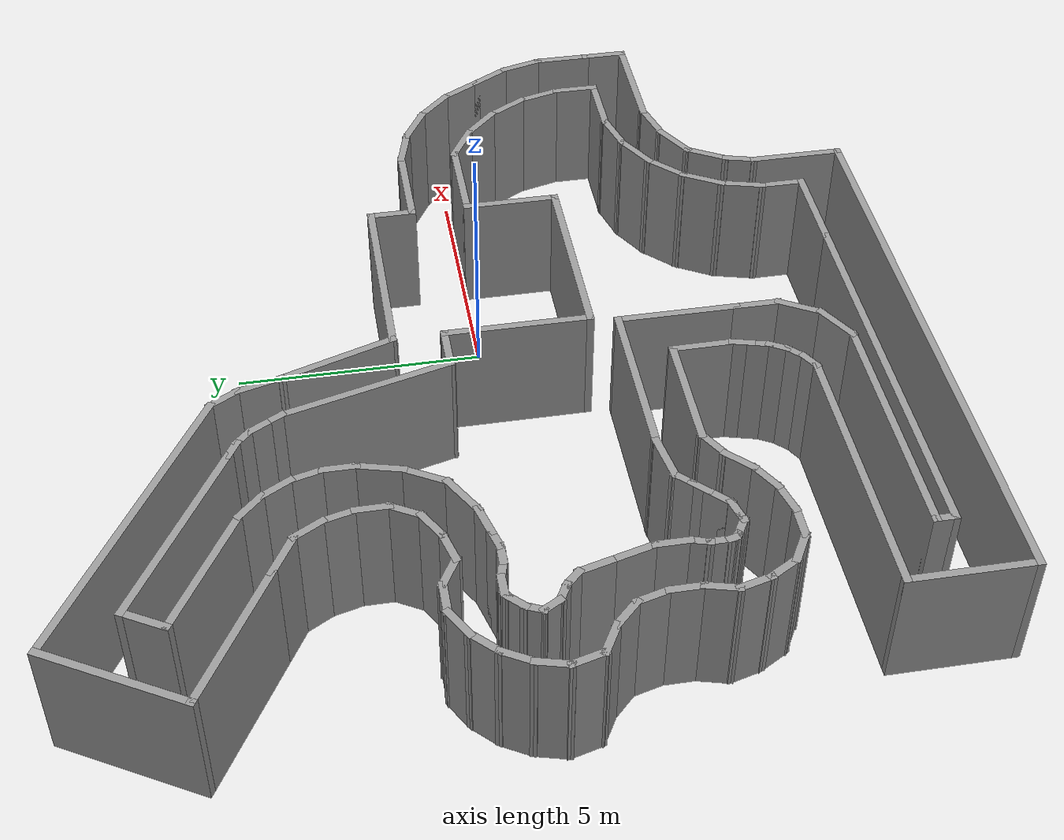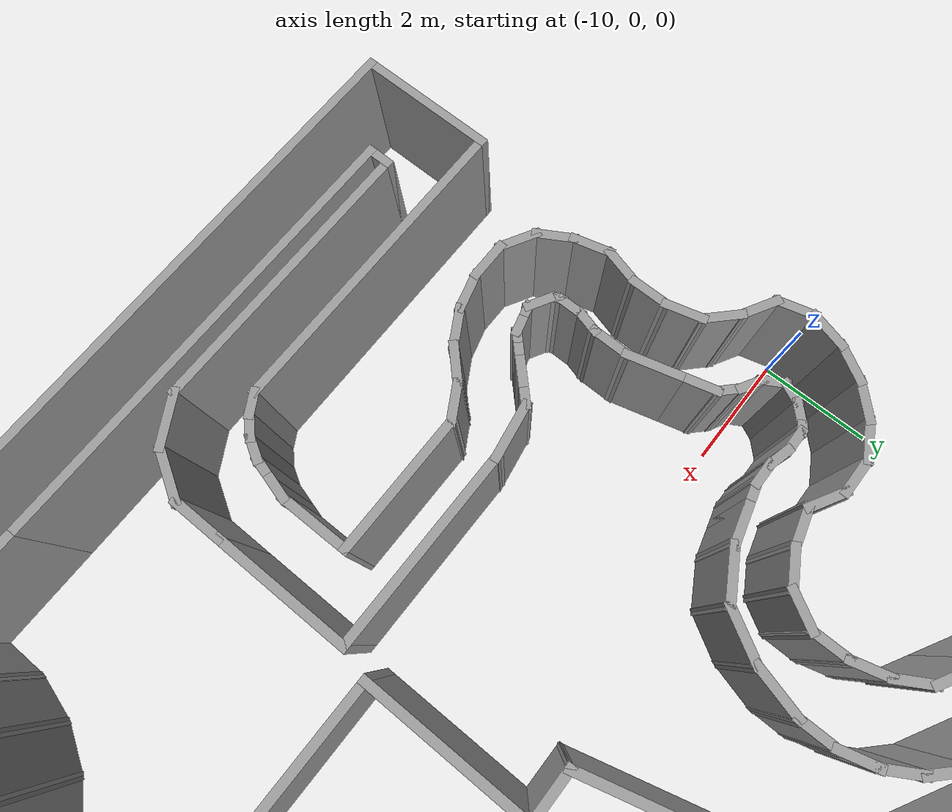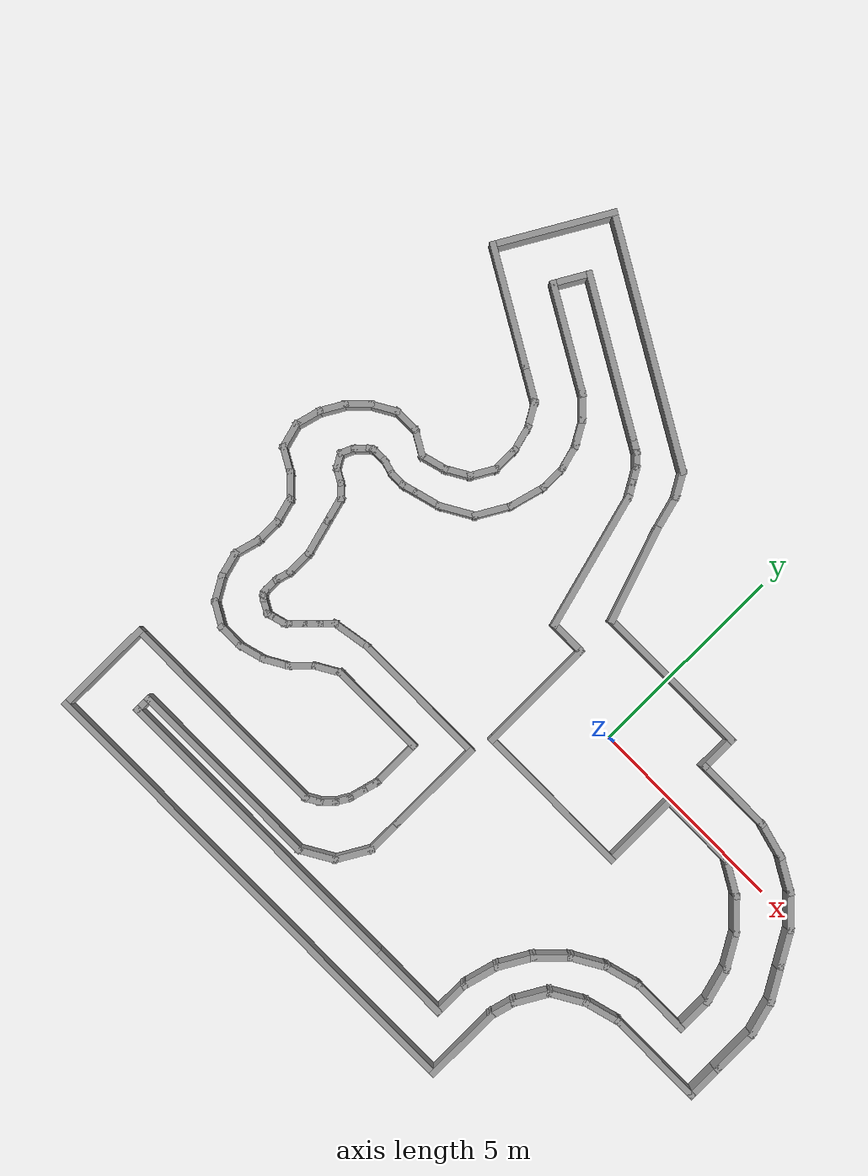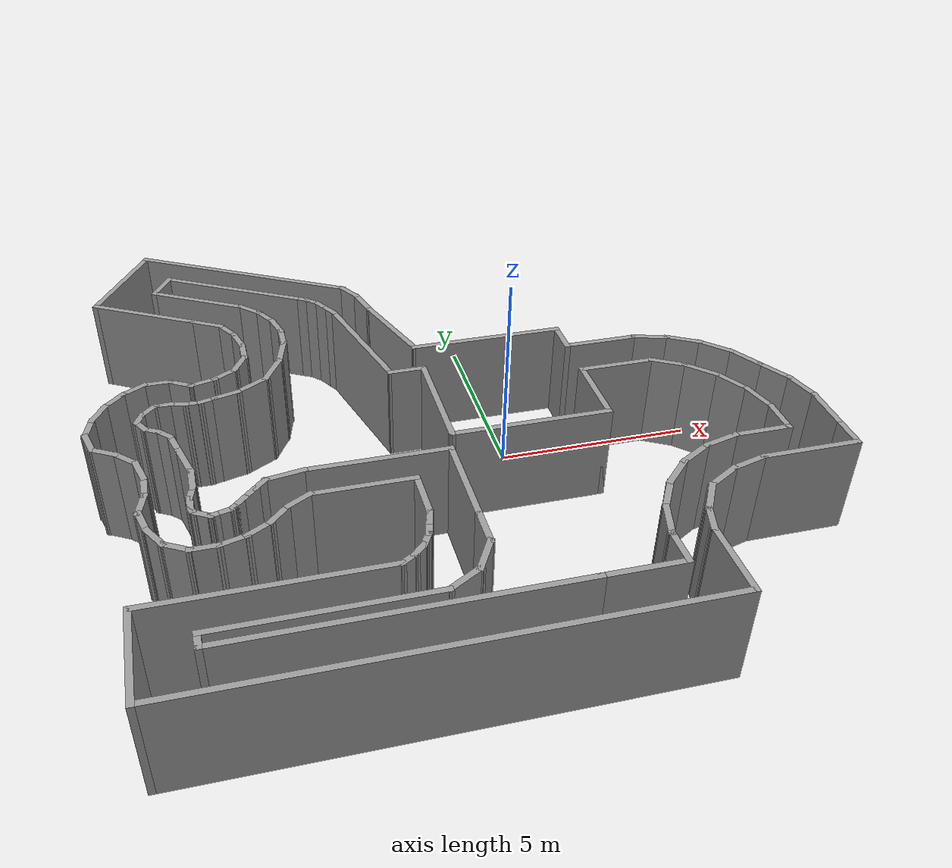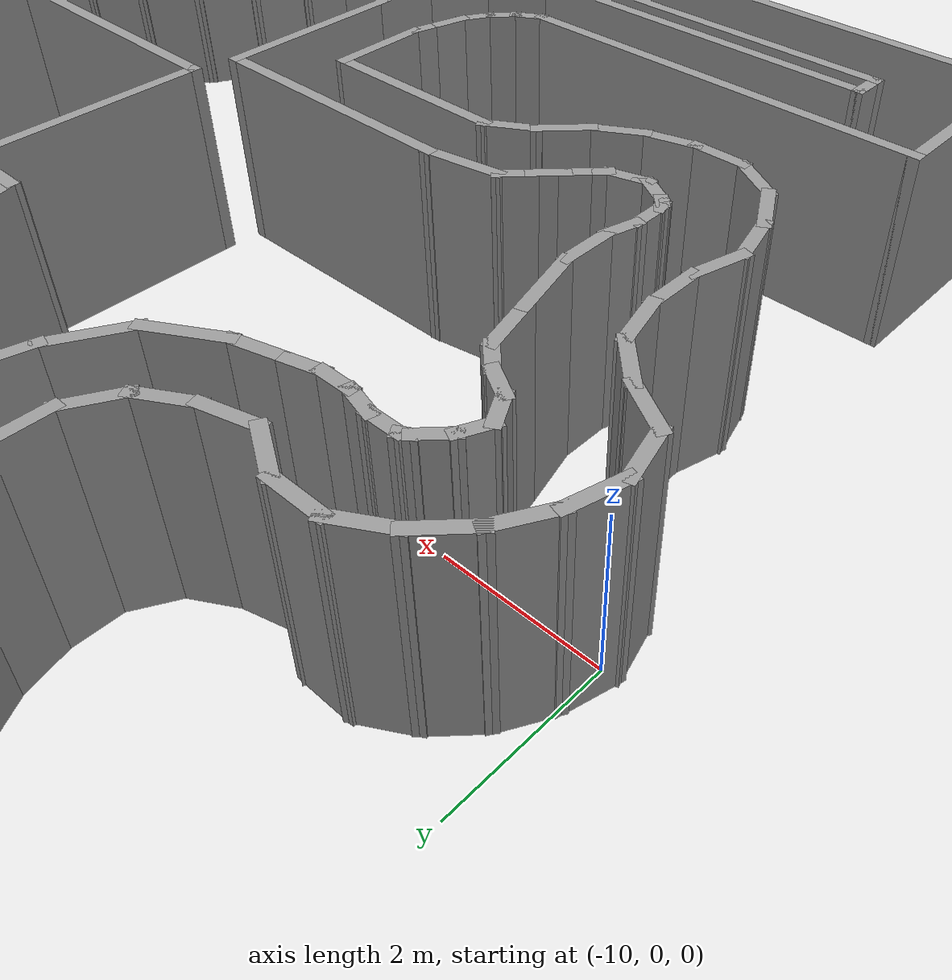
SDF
<?xml version='1.0'?>
<sdf version='1.7'>
  <model name='labirinth'>
    <pose>-1.55942 0.15521 0 0 -0 0</pose>
    <link name='Wall_100'>
      <collision name='Wall_100_Collision'>
        <geometry>
          <box>
            <size>0.75 0.15 2.5</size>
          </box>
        </geometry>
        <pose>0 0 1.25 0 -0 0</pose>
      </collision>
      <visual name='Wall_100_Visual'>
        <pose>0 0 1.25 0 -0 0</pose>
        <geometry>
          <box>
            <size>0.75 0.15 2.5</size>
          </box>
        </geometry>
        <material>
          <script>
            <uri>file://media/materials/scripts/gazebo.material</uri>
            <name>Gazebo/Grey</name>
          </script>
          <ambient>1 1 1 1</ambient>
        </material>
        <meta>
          <layer>0</layer>
        </meta>
      </visual>
      <pose>-4.80966 2.0706 0 0 -0 1.0472</pose>
    </link>
    <link name='Wall_101'>
      <collision name='Wall_101_Collision'>
        <geometry>
          <box>
            <size>0.75 0.15 2.5</size>
          </box>
        </geometry>
        <pose>0 0 1.25 0 -0 0</pose>
      </collision>
      <visual name='Wall_101_Visual'>
        <pose>0 0 1.25 0 -0 0</pose>
        <geometry>
          <box>
            <size>0.75 0.15 2.5</size>
          </box>
        </geometry>
        <material>
          <script>
            <uri>file://media/materials/scripts/gazebo.material</uri>
            <name>Gazebo/Grey</name>
          </script>
          <ambient>1 1 1 1</ambient>
        </material>
        <meta>
          <layer>0</layer>
        </meta>
      </visual>
      <pose>-4.65966 2.6304 0 0 -0 1.5708</pose>
    </link>
    <link name='Wall_102'>
      <collision name='Wall_102_Collision'>
        <geometry>
          <box>
            <size>0.75 0.15 2.5</size>
          </box>
        </geometry>
        <pose>0 0 1.25 0 -0 0</pose>
      </collision>
      <visual name='Wall_102_Visual'>
        <pose>0 0 1.25 0 -0 0</pose>
        <geometry>
          <box>
            <size>0.75 0.15 2.5</size>
          </box>
        </geometry>
        <material>
          <script>
            <uri>file://media/materials/scripts/gazebo.material</uri>
            <name>Gazebo/Grey</name>
          </script>
          <ambient>1 1 1 1</ambient>
        </material>
        <meta>
          <layer>0</layer>
        </meta>
      </visual>
      <pose>-4.73731 3.22018 0 0 -0 1.8326</pose>
    </link>
    <link name='Wall_103'>
      <collision name='Wall_103_Collision'>
        <geometry>
          <box>
            <size>0.75 0.15 2.5</size>
          </box>
        </geometry>
        <pose>0 0 1.25 0 -0 0</pose>
      </collision>
      <visual name='Wall_103_Visual'>
        <pose>0 0 1.25 0 -0 0</pose>
        <geometry>
          <box>
            <size>0.75 0.15 2.5</size>
          </box>
        </geometry>
        <material>
          <script>
            <uri>file://media/materials/scripts/gazebo.material</uri>
            <name>Gazebo/Grey</name>
          </script>
          <ambient>1 1 1 1</ambient>
        </material>
        <meta>
          <layer>0</layer>
        </meta>
      </visual>
      <pose>-4.96495 3.76977 0 0 -0 2.0944</pose>
    </link>
    <link name='Wall_104'>
      <collision name='Wall_104_Collision'>
        <geometry>
          <box>
            <size>1 0.15 2.5</size>
          </box>
        </geometry>
        <pose>0 0 1.25 0 -0 0</pose>
      </collision>
      <visual name='Wall_104_Visual'>
        <pose>0 0 1.25 0 -0 0</pose>
        <geometry>
          <box>
            <size>1 0.15 2.5</size>
          </box>
        </geometry>
        <material>
          <script>
            <uri>file://media/materials/scripts/gazebo.material</uri>
            <name>Gazebo/Grey</name>
          </script>
          <ambient>1 1 1 1</ambient>
        </material>
        <meta>
          <layer>0</layer>
        </meta>
      </visual>
      <pose>-5.48301 4.24207 0 0 -0 2.61799</pose>
    </link>
    <link name='Wall_105'>
      <collision name='Wall_105_Collision'>
        <geometry>
          <box>
            <size>3 0.15 2.5</size>
          </box>
        </geometry>
        <pose>0 0 1.25 0 -0 0</pose>
      </collision>
      <visual name='Wall_105_Visual'>
        <pose>0 0 1.25 0 -0 0</pose>
        <geometry>
          <box>
            <size>3 0.15 2.5</size>
          </box>
        </geometry>
        <material>
          <script>
            <uri>file://media/materials/scripts/gazebo.material</uri>
            <name>Gazebo/Grey</name>
          </script>
          <ambient>1 1 1 1</ambient>
        </material>
        <meta>
          <layer>0</layer>
        </meta>
      </visual>
      <pose>-7.08516 5.16707 0 0 -0 2.61799</pose>
    </link>
    <link name='Wall_106'>
      <collision name='Wall_106_Collision'>
        <geometry>
          <box>
            <size>3 0.15 2.5</size>
          </box>
        </geometry>
        <pose>0 0 1.25 0 -0 0</pose>
      </collision>
      <visual name='Wall_106_Visual'>
        <pose>0 0 1.25 0 -0 0</pose>
        <geometry>
          <box>
            <size>3 0.15 2.5</size>
          </box>
        </geometry>
        <material>
          <script>
            <uri>file://media/materials/scripts/gazebo.material</uri>
            <name>Gazebo/Grey</name>
          </script>
          <ambient>1 1 1 1</ambient>
        </material>
        <meta>
          <layer>0</layer>
        </meta>
      </visual>
      <pose>-7.60675 7.11366 0 0 -0 1.0472</pose>
    </link>
    <link name='Wall_107'>
      <collision name='Wall_107_Collision'>
        <geometry>
          <box>
            <size>6.25 0.15 2.5</size>
          </box>
        </geometry>
        <pose>0 0 1.25 0 -0 0</pose>
      </collision>
      <visual name='Wall_107_Visual'>
        <pose>0 0 1.25 0 -0 0</pose>
        <geometry>
          <box>
            <size>6.25 0.15 2.5</size>
          </box>
        </geometry>
        <material>
          <script>
            <uri>file://media/materials/scripts/gazebo.material</uri>
            <name>Gazebo/Grey</name>
          </script>
          <ambient>1 1 1 1</ambient>
        </material>
        <meta>
          <layer>0</layer>
        </meta>
      </visual>
      <pose>-4.25287 6.82275 0 0 -0 -0.523599</pose>
    </link>
    <link name='Wall_108'>
      <collision name='Wall_108_Collision'>
        <geometry>
          <box>
            <size>0.75 0.15 2.5</size>
          </box>
        </geometry>
        <pose>0 0 1.25 0 -0 0</pose>
      </collision>
      <visual name='Wall_108_Visual'>
        <pose>0 0 1.25 0 -0 0</pose>
        <geometry>
          <box>
            <size>0.75 0.15 2.5</size>
          </box>
        </geometry>
        <material>
          <script>
            <uri>file://media/materials/scripts/gazebo.material</uri>
            <name>Gazebo/Grey</name>
          </script>
          <ambient>1 1 1 1</ambient>
        </material>
        <meta>
          <layer>0</layer>
        </meta>
      </visual>
      <pose>-1.46149 5.03794 0 0 -0 -1.0472</pose>
    </link>
    <link name='Wall_109'>
      <collision name='Wall_109_Collision'>
        <geometry>
          <box>
            <size>1 0.15 2.5</size>
          </box>
        </geometry>
        <pose>0 0 1.25 0 -0 0</pose>
      </collision>
      <visual name='Wall_109_Visual'>
        <pose>0 0 1.25 0 -0 0</pose>
        <geometry>
          <box>
            <size>1 0.15 2.5</size>
          </box>
        </geometry>
        <material>
          <script>
            <uri>file://media/materials/scripts/gazebo.material</uri>
            <name>Gazebo/Grey</name>
          </script>
          <ambient>1 1 1 1</ambient>
        </material>
        <meta>
          <layer>0</layer>
        </meta>
      </visual>
      <pose>-1.20149 4.36761 0 0 -0 -1.309</pose>
    </link>
    <link name='Wall_11'>
      <collision name='Wall_11_Collision'>
        <geometry>
          <box>
            <size>1 0.15 2.5</size>
          </box>
        </geometry>
        <pose>0 0 1.25 0 -0 0</pose>
      </collision>
      <visual name='Wall_11_Visual'>
        <pose>0 0 1.25 0 -0 0</pose>
        <geometry>
          <box>
            <size>1 0.15 2.5</size>
          </box>
        </geometry>
        <material>
          <script>
            <uri>file://media/materials/scripts/gazebo.material</uri>
            <name>Gazebo/Grey</name>
          </script>
          <ambient>1 1 1 1</ambient>
        </material>
        <meta>
          <layer>0</layer>
        </meta>
      </visual>
      <pose>5.71748 -0.43771 0 0 -0 -0.523599</pose>
    </link>
    <link name='Wall_110'>
      <collision name='Wall_110_Collision'>
        <geometry>
          <box>
            <size>2.45465 0.15 2.5</size>
          </box>
        </geometry>
        <pose>0 0 1.25 0 -0 0</pose>
      </collision>
      <visual name='Wall_110_Visual'>
        <pose>0 0 1.25 0 -0 0</pose>
        <geometry>
          <box>
            <size>2.45465 0.15 2.5</size>
          </box>
        </geometry>
        <material>
          <script>
            <uri>file://media/materials/scripts/gazebo.material</uri>
            <name>Gazebo/Grey</name>
          </script>
          <ambient>1 1 1 1</ambient>
        </material>
        <meta>
          <layer>0</layer>
        </meta>
      </visual>
      <pose>-0.721037 2.86594 0 0 -0 -1.2435</pose>
    </link>
    <link name='Wall_112'>
      <collision name='Wall_112_Collision'>
        <geometry>
          <box>
            <size>3 0.15 2.5</size>
          </box>
        </geometry>
        <pose>0 0 1.25 0 -0 0</pose>
      </collision>
      <visual name='Wall_112_Visual'>
        <pose>0 0 1.25 0 -0 0</pose>
        <geometry>
          <box>
            <size>3 0.15 2.5</size>
          </box>
        </geometry>
        <material>
          <script>
            <uri>file://media/materials/scripts/gazebo.material</uri>
            <name>Gazebo/Grey</name>
          </script>
          <ambient>1 1 1 1</ambient>
        </material>
        <meta>
          <layer>0</layer>
        </meta>
      </visual>
      <pose>-0.350577 -0.65021 0 0 -0 1.5708</pose>
    </link>
    <link name='Wall_113'>
      <collision name='Wall_113_Collision'>
        <geometry>
          <box>
            <size>1 0.15 2.5</size>
          </box>
        </geometry>
        <pose>0 0 1.25 0 -0 0</pose>
      </collision>
      <visual name='Wall_113_Visual'>
        <pose>0 0 1.25 0 -0 0</pose>
        <geometry>
          <box>
            <size>1 0.15 2.5</size>
          </box>
        </geometry>
        <material>
          <script>
            <uri>file://media/materials/scripts/gazebo.material</uri>
            <name>Gazebo/Grey</name>
          </script>
          <ambient>1 1 1 1</ambient>
        </material>
        <meta>
          <layer>0</layer>
        </meta>
      </visual>
      <pose>-0.775577 0.77479 0 0 -0 3.14159</pose>
    </link>
    <link name='Wall_114'>
      <collision name='Wall_114_Collision'>
        <geometry>
          <box>
            <size>3.5 0.15 2.5</size>
          </box>
        </geometry>
        <pose>0 0 1.25 0 -0 0</pose>
      </collision>
      <visual name='Wall_114_Visual'>
        <pose>0 0 1.25 0 -0 0</pose>
        <geometry>
          <box>
            <size>3.5 0.15 2.5</size>
          </box>
        </geometry>
        <material>
          <script>
            <uri>file://media/materials/scripts/gazebo.material</uri>
            <name>Gazebo/Grey</name>
          </script>
          <ambient>1 1 1 1</ambient>
        </material>
        <meta>
          <layer>0</layer>
        </meta>
      </visual>
      <pose>-1.6341 2.39272 0 0 -0 1.8326</pose>
    </link>
    <link name='Wall_115'>
      <collision name='Wall_115_Collision'>
        <geometry>
          <box>
            <size>0.5 0.15 2.5</size>
          </box>
        </geometry>
        <pose>0 0 1.25 0 -0 0</pose>
      </collision>
      <visual name='Wall_115_Visual'>
        <pose>0 0 1.25 0 -0 0</pose>
        <geometry>
          <box>
            <size>0.5 0.15 2.5</size>
          </box>
        </geometry>
        <material>
          <script>
            <uri>file://media/materials/scripts/gazebo.material</uri>
            <name>Gazebo/Grey</name>
          </script>
          <ambient>1 1 1 1</ambient>
        </material>
        <meta>
          <layer>0</layer>
        </meta>
      </visual>
      <pose>-2.15512 4.1622 0 0 -0 2.0944</pose>
    </link>
    <link name='Wall_116'>
      <collision name='Wall_116_Collision'>
        <geometry>
          <box>
            <size>0.5 0.15 2.5</size>
          </box>
        </geometry>
        <pose>0 0 1.25 0 -0 0</pose>
      </collision>
      <visual name='Wall_116_Visual'>
        <pose>0 0 1.25 0 -0 0</pose>
        <geometry>
          <box>
            <size>0.5 0.15 2.5</size>
          </box>
        </geometry>
        <material>
          <script>
            <uri>file://media/materials/scripts/gazebo.material</uri>
            <name>Gazebo/Grey</name>
          </script>
          <ambient>1 1 1 1</ambient>
        </material>
        <meta>
          <layer>0</layer>
        </meta>
      </visual>
      <pose>-2.33012 4.4653 0 0 -0 2.0944</pose>
    </link>
    <link name='Wall_117'>
      <collision name='Wall_117_Collision'>
        <geometry>
          <box>
            <size>0.5 0.15 2.5</size>
          </box>
        </geometry>
        <pose>0 0 1.25 0 -0 0</pose>
      </collision>
      <visual name='Wall_117_Visual'>
        <pose>0 0 1.25 0 -0 0</pose>
        <geometry>
          <box>
            <size>0.5 0.15 2.5</size>
          </box>
        </geometry>
        <material>
          <script>
            <uri>file://media/materials/scripts/gazebo.material</uri>
            <name>Gazebo/Grey</name>
          </script>
          <ambient>1 1 1 1</ambient>
        </material>
        <meta>
          <layer>0</layer>
        </meta>
      </visual>
      <pose>-2.54136 4.7406 0 0 -0 2.35619</pose>
    </link>
    <link name='Wall_118'>
      <collision name='Wall_118_Collision'>
        <geometry>
          <box>
            <size>0.5 0.15 2.5</size>
          </box>
        </geometry>
        <pose>0 0 1.25 0 -0 0</pose>
      </collision>
      <visual name='Wall_118_Visual'>
        <pose>0 0 1.25 0 -0 0</pose>
        <geometry>
          <box>
            <size>0.5 0.15 2.5</size>
          </box>
        </geometry>
        <material>
          <script>
            <uri>file://media/materials/scripts/gazebo.material</uri>
            <name>Gazebo/Grey</name>
          </script>
          <ambient>1 1 1 1</ambient>
        </material>
        <meta>
          <layer>0</layer>
        </meta>
      </visual>
      <pose>-2.81666 4.95185 0 0 -0 2.61799</pose>
    </link>
    <link name='Wall_119'>
      <collision name='Wall_119_Collision'>
        <geometry>
          <box>
            <size>4 0.15 2.5</size>
          </box>
        </geometry>
        <pose>0 0 1.25 0 -0 0</pose>
      </collision>
      <visual name='Wall_119_Visual'>
        <pose>0 0 1.25 0 -0 0</pose>
        <geometry>
          <box>
            <size>4 0.15 2.5</size>
          </box>
        </geometry>
        <material>
          <script>
            <uri>file://media/materials/scripts/gazebo.material</uri>
            <name>Gazebo/Grey</name>
          </script>
          <ambient>1 1 1 1</ambient>
        </material>
        <meta>
          <layer>0</layer>
        </meta>
      </visual>
      <pose>-4.63532 6.00185 0 0 -0 2.61799</pose>
    </link>
    <link name='Wall_12'>
      <collision name='Wall_12_Collision'>
        <geometry>
          <box>
            <size>1 0.15 2.5</size>
          </box>
        </geometry>
        <pose>0 0 1.25 0 -0 0</pose>
      </collision>
      <visual name='Wall_12_Visual'>
        <pose>0 0 1.25 0 -0 0</pose>
        <geometry>
          <box>
            <size>1 0.15 2.5</size>
          </box>
        </geometry>
        <material>
          <script>
            <uri>file://media/materials/scripts/gazebo.material</uri>
            <name>Gazebo/Grey</name>
          </script>
          <ambient>1 1 1 1</ambient>
        </material>
        <meta>
          <layer>0</layer>
        </meta>
      </visual>
      <pose>6.38607 -0.95073 0 0 -0 -0.785398</pose>
    </link>
    <link name='Wall_120'>
      <collision name='Wall_120_Collision'>
        <geometry>
          <box>
            <size>1 0.15 2.5</size>
          </box>
        </geometry>
        <pose>0 0 1.25 0 -0 0</pose>
      </collision>
      <visual name='Wall_120_Visual'>
        <pose>0 0 1.25 0 -0 0</pose>
        <geometry>
          <box>
            <size>1 0.15 2.5</size>
          </box>
        </geometry>
        <material>
          <script>
            <uri>file://media/materials/scripts/gazebo.material</uri>
            <name>Gazebo/Grey</name>
          </script>
          <ambient>1 1 1 1</ambient>
        </material>
        <meta>
          <layer>0</layer>
        </meta>
      </visual>
      <pose>-6.51492 6.59629 0 0 -0 -2.0944</pose>
    </link>
    <link name='Wall_121'>
      <collision name='Wall_121_Collision'>
        <geometry>
          <box>
            <size>2.75 0.15 2.5</size>
          </box>
        </geometry>
        <pose>0 0 1.25 0 -0 0</pose>
      </collision>
      <visual name='Wall_121_Visual'>
        <pose>0 0 1.25 0 -0 0</pose>
        <geometry>
          <box>
            <size>2.75 0.15 2.5</size>
          </box>
        </geometry>
        <material>
          <script>
            <uri>file://media/materials/scripts/gazebo.material</uri>
            <name>Gazebo/Grey</name>
          </script>
          <ambient>1 1 1 1</ambient>
        </material>
        <meta>
          <layer>0</layer>
        </meta>
      </visual>
      <pose>-5.60158 5.57823 0 0 -0 -0.523599</pose>
    </link>
    <link name='Wall_122'>
      <collision name='Wall_122_Collision'>
        <geometry>
          <box>
            <size>0.75 0.15 2.5</size>
          </box>
        </geometry>
        <pose>0 0 1.25 0 -0 0</pose>
      </collision>
      <visual name='Wall_122_Visual'>
        <pose>0 0 1.25 0 -0 0</pose>
        <geometry>
          <box>
            <size>0.75 0.15 2.5</size>
          </box>
        </geometry>
        <material>
          <script>
            <uri>file://media/materials/scripts/gazebo.material</uri>
            <name>Gazebo/Grey</name>
          </script>
          <ambient>1 1 1 1</ambient>
        </material>
        <meta>
          <layer>0</layer>
        </meta>
      </visual>
      <pose>-4.26362 4.71609 0 0 -0 -0.785398</pose>
    </link>
    <link name='Wall_123'>
      <collision name='Wall_123_Collision'>
        <geometry>
          <box>
            <size>0.75 0.15 2.5</size>
          </box>
        </geometry>
        <pose>0 0 1.25 0 -0 0</pose>
      </collision>
      <visual name='Wall_123_Visual'>
        <pose>0 0 1.25 0 -0 0</pose>
        <geometry>
          <box>
            <size>0.75 0.15 2.5</size>
          </box>
        </geometry>
        <material>
          <script>
            <uri>file://media/materials/scripts/gazebo.material</uri>
            <name>Gazebo/Grey</name>
          </script>
          <ambient>1 1 1 1</ambient>
        </material>
        <meta>
          <layer>0</layer>
        </meta>
      </visual>
      <pose>-3.90148 4.24415 0 0 -0 -1.0472</pose>
    </link>
    <link name='Wall_124'>
      <collision name='Wall_124_Collision'>
        <geometry>
          <box>
            <size>0.75 0.15 2.5</size>
          </box>
        </geometry>
        <pose>0 0 1.25 0 -0 0</pose>
      </collision>
      <visual name='Wall_124_Visual'>
        <pose>0 0 1.25 0 -0 0</pose>
        <geometry>
          <box>
            <size>0.75 0.15 2.5</size>
          </box>
        </geometry>
        <material>
          <script>
            <uri>file://media/materials/scripts/gazebo.material</uri>
            <name>Gazebo/Grey</name>
          </script>
          <ambient>1 1 1 1</ambient>
        </material>
        <meta>
          <layer>0</layer>
        </meta>
      </visual>
      <pose>-3.67384 3.69457 0 0 -0 -1.309</pose>
    </link>
    <link name='Wall_125'>
      <collision name='Wall_125_Collision'>
        <geometry>
          <box>
            <size>0.75 0.15 2.5</size>
          </box>
        </geometry>
        <pose>0 0 1.25 0 -0 0</pose>
      </collision>
      <visual name='Wall_125_Visual'>
        <pose>0 0 1.25 0 -0 0</pose>
        <geometry>
          <box>
            <size>0.75 0.15 2.5</size>
          </box>
        </geometry>
        <material>
          <script>
            <uri>file://media/materials/scripts/gazebo.material</uri>
            <name>Gazebo/Grey</name>
          </script>
          <ambient>1 1 1 1</ambient>
        </material>
        <meta>
          <layer>0</layer>
        </meta>
      </visual>
      <pose>-3.59619 3.10479 0 0 -0 -1.5708</pose>
    </link>
    <link name='Wall_126'>
      <collision name='Wall_126_Collision'>
        <geometry>
          <box>
            <size>1 0.15 2.5</size>
          </box>
        </geometry>
        <pose>0 0 1.25 0 -0 0</pose>
      </collision>
      <visual name='Wall_126_Visual'>
        <pose>0 0 1.25 0 -0 0</pose>
        <geometry>
          <box>
            <size>1 0.15 2.5</size>
          </box>
        </geometry>
        <material>
          <script>
            <uri>file://media/materials/scripts/gazebo.material</uri>
            <name>Gazebo/Grey</name>
          </script>
          <ambient>1 1 1 1</ambient>
        </material>
        <meta>
          <layer>0</layer>
        </meta>
      </visual>
      <pose>-3.70619 2.39427 0 0 -0 -1.8326</pose>
    </link>
    <link name='Wall_127'>
      <collision name='Wall_127_Collision'>
        <geometry>
          <box>
            <size>1 0.15 2.5</size>
          </box>
        </geometry>
        <pose>0 0 1.25 0 -0 0</pose>
      </collision>
      <visual name='Wall_127_Visual'>
        <pose>0 0 1.25 0 -0 0</pose>
        <geometry>
          <box>
            <size>1 0.15 2.5</size>
          </box>
        </geometry>
        <material>
          <script>
            <uri>file://media/materials/scripts/gazebo.material</uri>
            <name>Gazebo/Grey</name>
          </script>
          <ambient>1 1 1 1</ambient>
        </material>
        <meta>
          <layer>0</layer>
        </meta>
      </visual>
      <pose>-4.02869 1.61569 0 0 -0 -2.0944</pose>
    </link>
    <link name='Wall_128'>
      <collision name='Wall_128_Collision'>
        <geometry>
          <box>
            <size>1 0.15 2.5</size>
          </box>
        </geometry>
        <pose>0 0 1.25 0 -0 0</pose>
      </collision>
      <visual name='Wall_128_Visual'>
        <pose>0 0 1.25 0 -0 0</pose>
        <geometry>
          <box>
            <size>1 0.15 2.5</size>
          </box>
        </geometry>
        <material>
          <script>
            <uri>file://media/materials/scripts/gazebo.material</uri>
            <name>Gazebo/Grey</name>
          </script>
          <ambient>1 1 1 1</ambient>
        </material>
        <meta>
          <layer>0</layer>
        </meta>
      </visual>
      <pose>-4.60925 1.03513 0 0 -0 -2.61799</pose>
    </link>
    <link name='Wall_129'>
      <collision name='Wall_129_Collision'>
        <geometry>
          <box>
            <size>0.75 0.15 2.5</size>
          </box>
        </geometry>
        <pose>0 0 1.25 0 -0 0</pose>
      </collision>
      <visual name='Wall_129_Visual'>
        <pose>0 0 1.25 0 -0 0</pose>
        <geometry>
          <box>
            <size>0.75 0.15 2.5</size>
          </box>
        </geometry>
        <material>
          <script>
            <uri>file://media/materials/scripts/gazebo.material</uri>
            <name>Gazebo/Grey</name>
          </script>
          <ambient>1 1 1 1</ambient>
        </material>
        <meta>
          <layer>0</layer>
        </meta>
      </visual>
      <pose>-5.26709 0.744986 0 0 -0 -2.87979</pose>
    </link>
    <link name='Wall_13'>
      <collision name='Wall_13_Collision'>
        <geometry>
          <box>
            <size>1 0.15 2.5</size>
          </box>
        </geometry>
        <pose>0 0 1.25 0 -0 0</pose>
      </collision>
      <visual name='Wall_13_Visual'>
        <pose>0 0 1.25 0 -0 0</pose>
        <geometry>
          <box>
            <size>1 0.15 2.5</size>
          </box>
        </geometry>
        <material>
          <script>
            <uri>file://media/materials/scripts/gazebo.material</uri>
            <name>Gazebo/Grey</name>
          </script>
          <ambient>1 1 1 1</ambient>
        </material>
        <meta>
          <layer>0</layer>
        </meta>
      </visual>
      <pose>6.89909 -1.61931 0 0 -0 -1.0472</pose>
    </link>
    <link name='Wall_130'>
      <collision name='Wall_130_Collision'>
        <geometry>
          <box>
            <size>0.5 0.15 2.5</size>
          </box>
        </geometry>
        <pose>0 0 1.25 0 -0 0</pose>
      </collision>
      <visual name='Wall_130_Visual'>
        <pose>0 0 1.25 0 -0 0</pose>
        <geometry>
          <box>
            <size>0.5 0.15 2.5</size>
          </box>
        </geometry>
        <material>
          <script>
            <uri>file://media/materials/scripts/gazebo.material</uri>
            <name>Gazebo/Grey</name>
          </script>
          <ambient>1 1 1 1</ambient>
        </material>
        <meta>
          <layer>0</layer>
        </meta>
      </visual>
      <pose>-5.7259 0.622047 0 0 -0 -2.87979</pose>
    </link>
    <link name='Wall_132'>
      <collision name='Wall_132_Collision'>
        <geometry>
          <box>
            <size>0.5 0.15 2.5</size>
          </box>
        </geometry>
        <pose>0 0 1.25 0 -0 0</pose>
      </collision>
      <visual name='Wall_132_Visual'>
        <pose>0 0 1.25 0 -0 0</pose>
        <geometry>
          <box>
            <size>0.5 0.15 2.5</size>
          </box>
        </geometry>
        <material>
          <script>
            <uri>file://media/materials/scripts/gazebo.material</uri>
            <name>Gazebo/Grey</name>
          </script>
          <ambient>1 1 1 1</ambient>
        </material>
        <meta>
          <layer>0</layer>
        </meta>
      </visual>
      <pose>-6.06994 0.576754 0 0 -0 3.14159</pose>
    </link>
    <link name='Wall_133'>
      <collision name='Wall_133_Collision'>
        <geometry>
          <box>
            <size>0.5 0.15 2.5</size>
          </box>
        </geometry>
        <pose>0 0 1.25 0 -0 0</pose>
      </collision>
      <visual name='Wall_133_Visual'>
        <pose>0 0 1.25 0 -0 0</pose>
        <geometry>
          <box>
            <size>0.5 0.15 2.5</size>
          </box>
        </geometry>
        <material>
          <script>
            <uri>file://media/materials/scripts/gazebo.material</uri>
            <name>Gazebo/Grey</name>
          </script>
          <ambient>1 1 1 1</ambient>
        </material>
        <meta>
          <layer>0</layer>
        </meta>
      </visual>
      <pose>-6.41398 0.622047 0 0 -0 2.87979</pose>
    </link>
    <link name='Wall_134'>
      <collision name='Wall_134_Collision'>
        <geometry>
          <box>
            <size>0.5 0.15 2.5</size>
          </box>
        </geometry>
        <pose>0 0 1.25 0 -0 0</pose>
      </collision>
      <visual name='Wall_134_Visual'>
        <pose>0 0 1.25 0 -0 0</pose>
        <geometry>
          <box>
            <size>0.5 0.15 2.5</size>
          </box>
        </geometry>
        <material>
          <script>
            <uri>file://media/materials/scripts/gazebo.material</uri>
            <name>Gazebo/Grey</name>
          </script>
          <ambient>1 1 1 1</ambient>
        </material>
        <meta>
          <layer>0</layer>
        </meta>
      </visual>
      <pose>-6.75802 0.667341 0 0 -0 3.14159</pose>
    </link>
    <link name='Wall_135'>
      <collision name='Wall_135_Collision'>
        <geometry>
          <box>
            <size>0.25 0.15 2.5</size>
          </box>
        </geometry>
        <pose>0 0 1.25 0 -0 0</pose>
      </collision>
      <visual name='Wall_135_Visual'>
        <pose>0 0 1.25 0 -0 0</pose>
        <geometry>
          <box>
            <size>0.25 0.15 2.5</size>
          </box>
        </geometry>
        <material>
          <script>
            <uri>file://media/materials/scripts/gazebo.material</uri>
            <name>Gazebo/Grey</name>
          </script>
          <ambient>1 1 1 1</ambient>
        </material>
        <meta>
          <layer>0</layer>
        </meta>
      </visual>
      <pose>-6.97631 0.642341 0 0 -0 -2.61799</pose>
    </link>
    <link name='Wall_136'>
      <collision name='Wall_136_Collision'>
        <geometry>
          <box>
            <size>0.5 0.15 2.5</size>
          </box>
        </geometry>
        <pose>0 0 1.25 0 -0 0</pose>
      </collision>
      <visual name='Wall_136_Visual'>
        <pose>0 0 1.25 0 -0 0</pose>
        <geometry>
          <box>
            <size>0.5 0.15 2.5</size>
          </box>
        </geometry>
        <material>
          <script>
            <uri>file://media/materials/scripts/gazebo.material</uri>
            <name>Gazebo/Grey</name>
          </script>
          <ambient>1 1 1 1</ambient>
        </material>
        <meta>
          <layer>0</layer>
        </meta>
      </visual>
      <pose>-7.14336 0.493597 0 0 -0 -2.35619</pose>
    </link>
    <link name='Wall_137'>
      <collision name='Wall_137_Collision'>
        <geometry>
          <box>
            <size>0.469915 0.15 2.5</size>
          </box>
        </geometry>
        <pose>0 0 1.25 0 -0 0</pose>
      </collision>
      <visual name='Wall_137_Visual'>
        <pose>0 0 1.25 0 -0 0</pose>
        <geometry>
          <box>
            <size>0.469915 0.15 2.5</size>
          </box>
        </geometry>
        <material>
          <script>
            <uri>file://media/materials/scripts/gazebo.material</uri>
            <name>Gazebo/Grey</name>
          </script>
          <ambient>1 1 1 1</ambient>
        </material>
        <meta>
          <layer>0</layer>
        </meta>
      </visual>
      <pose>-7.33477 0.224911 0 0 -0 -2.00755</pose>
    </link>
    <link name='Wall_14'>
      <collision name='Wall_14_Collision'>
        <geometry>
          <box>
            <size>1 0.15 2.5</size>
          </box>
        </geometry>
        <pose>0 0 1.25 0 -0 0</pose>
      </collision>
      <visual name='Wall_14_Visual'>
        <pose>0 0 1.25 0 -0 0</pose>
        <geometry>
          <box>
            <size>1 0.15 2.5</size>
          </box>
        </geometry>
        <material>
          <script>
            <uri>file://media/materials/scripts/gazebo.material</uri>
            <name>Gazebo/Grey</name>
          </script>
          <ambient>1 1 1 1</ambient>
        </material>
        <meta>
          <layer>0</layer>
        </meta>
      </visual>
      <pose>7.22158 -2.39789 0 0 -0 -1.309</pose>
    </link>
    <link name='Wall_140'>
      <collision name='Wall_140_Collision'>
        <geometry>
          <box>
            <size>0.5 0.15 2.5</size>
          </box>
        </geometry>
        <pose>0 0 1.25 0 -0 0</pose>
      </collision>
      <visual name='Wall_140_Visual'>
        <pose>0 0 1.25 0 -0 0</pose>
        <geometry>
          <box>
            <size>0.5 0.15 2.5</size>
          </box>
        </geometry>
        <material>
          <script>
            <uri>file://media/materials/scripts/gazebo.material</uri>
            <name>Gazebo/Grey</name>
          </script>
          <ambient>1 1 1 1</ambient>
        </material>
        <meta>
          <layer>0</layer>
        </meta>
      </visual>
      <pose>-7.31493 -0.071585 0 0 -0 -1.0472</pose>
    </link>
    <link name='Wall_141'>
      <collision name='Wall_141_Collision'>
        <geometry>
          <box>
            <size>0.5 0.15 2.5</size>
          </box>
        </geometry>
        <pose>0 0 1.25 0 -0 0</pose>
      </collision>
      <visual name='Wall_141_Visual'>
        <pose>0 0 1.25 0 -0 0</pose>
        <geometry>
          <box>
            <size>0.5 0.15 2.5</size>
          </box>
        </geometry>
        <material>
          <script>
            <uri>file://media/materials/scripts/gazebo.material</uri>
            <name>Gazebo/Grey</name>
          </script>
          <ambient>1 1 1 1</ambient>
        </material>
        <meta>
          <layer>0</layer>
        </meta>
      </visual>
      <pose>-7.07587 -0.310639 0 0 -0 -0.523599</pose>
    </link>
    <link name='Wall_142'>
      <collision name='Wall_142_Collision'>
        <geometry>
          <box>
            <size>0.5 0.15 2.5</size>
          </box>
        </geometry>
        <pose>0 0 1.25 0 -0 0</pose>
      </collision>
      <visual name='Wall_142_Visual'>
        <pose>0 0 1.25 0 -0 0</pose>
        <geometry>
          <box>
            <size>0.5 0.15 2.5</size>
          </box>
        </geometry>
        <material>
          <script>
            <uri>file://media/materials/scripts/gazebo.material</uri>
            <name>Gazebo/Grey</name>
          </script>
          <ambient>1 1 1 1</ambient>
        </material>
        <meta>
          <layer>0</layer>
        </meta>
      </visual>
      <pose>-6.80058 -0.521883 0 0 -0 -0.785398</pose>
    </link>
    <link name='Wall_143'>
      <collision name='Wall_143_Collision'>
        <geometry>
          <box>
            <size>0.75 0.15 2.5</size>
          </box>
        </geometry>
        <pose>0 0 1.25 0 -0 0</pose>
      </collision>
      <visual name='Wall_143_Visual'>
        <pose>0 0 1.25 0 -0 0</pose>
        <geometry>
          <box>
            <size>0.75 0.15 2.5</size>
          </box>
        </geometry>
        <material>
          <script>
            <uri>file://media/materials/scripts/gazebo.material</uri>
            <name>Gazebo/Grey</name>
          </script>
          <ambient>1 1 1 1</ambient>
        </material>
        <meta>
          <layer>0</layer>
        </meta>
      </visual>
      <pose>-6.59919 -0.935405 0 0 -0 -1.309</pose>
    </link>
    <link name='Wall_144'>
      <collision name='Wall_144_Collision'>
        <geometry>
          <box>
            <size>1 0.15 2.5</size>
          </box>
        </geometry>
        <pose>0 0 1.25 0 -0 0</pose>
      </collision>
      <visual name='Wall_144_Visual'>
        <pose>0 0 1.25 0 -0 0</pose>
        <geometry>
          <box>
            <size>1 0.15 2.5</size>
          </box>
        </geometry>
        <material>
          <script>
            <uri>file://media/materials/scripts/gazebo.material</uri>
            <name>Gazebo/Grey</name>
          </script>
          <ambient>1 1 1 1</ambient>
        </material>
        <meta>
          <layer>0</layer>
        </meta>
      </visual>
      <pose>-6.41154 -1.6357 0 0 -0 -1.309</pose>
    </link>
    <link name='Wall_145'>
      <collision name='Wall_145_Collision'>
        <geometry>
          <box>
            <size>0.75 0.15 2.5</size>
          </box>
        </geometry>
        <pose>0 0 1.25 0 -0 0</pose>
      </collision>
      <visual name='Wall_145_Visual'>
        <pose>0 0 1.25 0 -0 0</pose>
        <geometry>
          <box>
            <size>0.75 0.15 2.5</size>
          </box>
        </geometry>
        <material>
          <script>
            <uri>file://media/materials/scripts/gazebo.material</uri>
            <name>Gazebo/Grey</name>
          </script>
          <ambient>1 1 1 1</ambient>
        </material>
        <meta>
          <layer>0</layer>
        </meta>
      </visual>
      <pose>-6.30154 -2.34622 0 0 -0 -1.5708</pose>
    </link>
    <link name='Wall_146'>
      <collision name='Wall_146_Collision'>
        <geometry>
          <box>
            <size>0.5 0.15 2.5</size>
          </box>
        </geometry>
        <pose>0 0 1.25 0 -0 0</pose>
      </collision>
      <visual name='Wall_146_Visual'>
        <pose>0 0 1.25 0 -0 0</pose>
        <geometry>
          <box>
            <size>0.5 0.15 2.5</size>
          </box>
        </geometry>
        <material>
          <script>
            <uri>file://media/materials/scripts/gazebo.material</uri>
            <name>Gazebo/Grey</name>
          </script>
          <ambient>1 1 1 1</ambient>
        </material>
        <meta>
          <layer>0</layer>
        </meta>
      </visual>
      <pose>-6.34684 -2.81526 0 0 -0 -1.8326</pose>
    </link>
    <link name='Wall_147'>
      <collision name='Wall_147_Collision'>
        <geometry>
          <box>
            <size>0.5 0.15 2.5</size>
          </box>
        </geometry>
        <pose>0 0 1.25 0 -0 0</pose>
      </collision>
      <visual name='Wall_147_Visual'>
        <pose>0 0 1.25 0 -0 0</pose>
        <geometry>
          <box>
            <size>0.5 0.15 2.5</size>
          </box>
        </geometry>
        <material>
          <script>
            <uri>file://media/materials/scripts/gazebo.material</uri>
            <name>Gazebo/Grey</name>
          </script>
          <ambient>1 1 1 1</ambient>
        </material>
        <meta>
          <layer>0</layer>
        </meta>
      </visual>
      <pose>-6.39213 -3.15929 0 0 -0 -1.5708</pose>
    </link>
    <link name='Wall_148'>
      <collision name='Wall_148_Collision'>
        <geometry>
          <box>
            <size>0.25 0.15 2.5</size>
          </box>
        </geometry>
        <pose>0 0 1.25 0 -0 0</pose>
      </collision>
      <visual name='Wall_148_Visual'>
        <pose>0 0 1.25 0 -0 0</pose>
        <geometry>
          <box>
            <size>0.25 0.15 2.5</size>
          </box>
        </geometry>
        <material>
          <script>
            <uri>file://media/materials/scripts/gazebo.material</uri>
            <name>Gazebo/Grey</name>
          </script>
          <ambient>1 1 1 1</ambient>
        </material>
        <meta>
          <layer>0</layer>
        </meta>
      </visual>
      <pose>-6.37919 -3.38259 0 0 -0 -1.309</pose>
    </link>
    <link name='Wall_149'>
      <collision name='Wall_149_Collision'>
        <geometry>
          <box>
            <size>0.25 0.15 2.5</size>
          </box>
        </geometry>
        <pose>0 0 1.25 0 -0 0</pose>
      </collision>
      <visual name='Wall_149_Visual'>
        <pose>0 0 1.25 0 -0 0</pose>
        <geometry>
          <box>
            <size>0.25 0.15 2.5</size>
          </box>
        </geometry>
        <material>
          <script>
            <uri>file://media/materials/scripts/gazebo.material</uri>
            <name>Gazebo/Grey</name>
          </script>
          <ambient>1 1 1 1</ambient>
        </material>
        <meta>
          <layer>0</layer>
        </meta>
      </visual>
      <pose>-6.33089 -3.46624 0 0 -0 -0.785398</pose>
    </link>
    <link name='Wall_15'>
      <collision name='Wall_15_Collision'>
        <geometry>
          <box>
            <size>1 0.15 2.5</size>
          </box>
        </geometry>
        <pose>0 0 1.25 0 -0 0</pose>
      </collision>
      <visual name='Wall_15_Visual'>
        <pose>0 0 1.25 0 -0 0</pose>
        <geometry>
          <box>
            <size>1 0.15 2.5</size>
          </box>
        </geometry>
        <material>
          <script>
            <uri>file://media/materials/scripts/gazebo.material</uri>
            <name>Gazebo/Grey</name>
          </script>
          <ambient>1 1 1 1</ambient>
        </material>
        <meta>
          <layer>0</layer>
        </meta>
      </visual>
      <pose>7.33158 -3.23341 0 0 -0 -1.5708</pose>
    </link>
    <link name='Wall_150'>
      <collision name='Wall_150_Collision'>
        <geometry>
          <box>
            <size>0.5 0.15 2.5</size>
          </box>
        </geometry>
        <pose>0 0 1.25 0 -0 0</pose>
      </collision>
      <visual name='Wall_150_Visual'>
        <pose>0 0 1.25 0 -0 0</pose>
        <geometry>
          <box>
            <size>0.5 0.15 2.5</size>
          </box>
        </geometry>
        <material>
          <script>
            <uri>file://media/materials/scripts/gazebo.material</uri>
            <name>Gazebo/Grey</name>
          </script>
          <ambient>1 1 1 1</ambient>
        </material>
        <meta>
          <layer>0</layer>
        </meta>
      </visual>
      <pose>-6.14398 -3.5891 0 0 -0 -0.523599</pose>
    </link>
    <link name='Wall_151'>
      <collision name='Wall_151_Collision'>
        <geometry>
          <box>
            <size>0.15 0.15 2.5</size>
          </box>
        </geometry>
        <pose>0 0 1.25 0 -0 0</pose>
      </collision>
      <visual name='Wall_151_Visual'>
        <pose>0 0 1.25 0 -0 0</pose>
        <geometry>
          <box>
            <size>0.15 0.15 2.5</size>
          </box>
        </geometry>
        <material>
          <script>
            <uri>file://media/materials/scripts/gazebo.material</uri>
            <name>Gazebo/Grey</name>
          </script>
          <ambient>1 1 1 1</ambient>
        </material>
        <meta>
          <layer>0</layer>
        </meta>
      </visual>
      <pose>-5.99243 -3.6766 0 0 -0 0</pose>
    </link>
    <link name='Wall_152'>
      <collision name='Wall_152_Collision'>
        <geometry>
          <box>
            <size>0.25 0.15 2.5</size>
          </box>
        </geometry>
        <pose>0 0 1.25 0 -0 0</pose>
      </collision>
      <visual name='Wall_152_Visual'>
        <pose>0 0 1.25 0 -0 0</pose>
        <geometry>
          <box>
            <size>0.25 0.15 2.5</size>
          </box>
        </geometry>
        <material>
          <script>
            <uri>file://media/materials/scripts/gazebo.material</uri>
            <name>Gazebo/Grey</name>
          </script>
          <ambient>1 1 1 1</ambient>
        </material>
        <meta>
          <layer>0</layer>
        </meta>
      </visual>
      <pose>-5.94413 -3.66366 0 0 -0 0.261799</pose>
    </link>
    <link name='Wall_153'>
      <collision name='Wall_153_Collision'>
        <geometry>
          <box>
            <size>0.5 0.15 2.5</size>
          </box>
        </geometry>
        <pose>0 0 1.25 0 -0 0</pose>
      </collision>
      <visual name='Wall_153_Visual'>
        <pose>0 0 1.25 0 -0 0</pose>
        <geometry>
          <box>
            <size>0.5 0.15 2.5</size>
          </box>
        </geometry>
        <material>
          <script>
            <uri>file://media/materials/scripts/gazebo.material</uri>
            <name>Gazebo/Grey</name>
          </script>
          <ambient>1 1 1 1</ambient>
        </material>
        <meta>
          <layer>0</layer>
        </meta>
      </visual>
      <pose>-5.7268 -3.60542 0 0 -0 0.261799</pose>
    </link>
    <link name='Wall_154'>
      <collision name='Wall_154_Collision'>
        <geometry>
          <box>
            <size>0.25 0.15 2.5</size>
          </box>
        </geometry>
        <pose>0 0 1.25 0 -0 0</pose>
      </collision>
      <visual name='Wall_154_Visual'>
        <pose>0 0 1.25 0 -0 0</pose>
        <geometry>
          <box>
            <size>0.25 0.15 2.5</size>
          </box>
        </geometry>
        <material>
          <script>
            <uri>file://media/materials/scripts/gazebo.material</uri>
            <name>Gazebo/Grey</name>
          </script>
          <ambient>1 1 1 1</ambient>
        </material>
        <meta>
          <layer>0</layer>
        </meta>
      </visual>
      <pose>-5.52241 -3.52477 0 0 -0 0.785398</pose>
    </link>
    <link name='Wall_155'>
      <collision name='Wall_155_Collision'>
        <geometry>
          <box>
            <size>0.5 0.15 2.5</size>
          </box>
        </geometry>
        <pose>0 0 1.25 0 -0 0</pose>
      </collision>
      <visual name='Wall_155_Visual'>
        <pose>0 0 1.25 0 -0 0</pose>
        <geometry>
          <box>
            <size>0.5 0.15 2.5</size>
          </box>
        </geometry>
        <material>
          <script>
            <uri>file://media/materials/scripts/gazebo.material</uri>
            <name>Gazebo/Grey</name>
          </script>
          <ambient>1 1 1 1</ambient>
        </material>
        <meta>
          <layer>0</layer>
        </meta>
      </visual>
      <pose>-5.36331 -3.36567 0 0 -0 0.785398</pose>
    </link>
    <link name='Wall_156'>
      <collision name='Wall_156_Collision'>
        <geometry>
          <box>
            <size>0.5 0.15 2.5</size>
          </box>
        </geometry>
        <pose>0 0 1.25 0 -0 0</pose>
      </collision>
      <visual name='Wall_156_Visual'>
        <pose>0 0 1.25 0 -0 0</pose>
        <geometry>
          <box>
            <size>0.5 0.15 2.5</size>
          </box>
        </geometry>
        <material>
          <script>
            <uri>file://media/materials/scripts/gazebo.material</uri>
            <name>Gazebo/Grey</name>
          </script>
          <ambient>1 1 1 1</ambient>
        </material>
        <meta>
          <layer>0</layer>
        </meta>
      </visual>
      <pose>-5.11582 -3.11819 0 0 -0 0.785398</pose>
    </link>
    <link name='Wall_157'>
      <collision name='Wall_157_Collision'>
        <geometry>
          <box>
            <size>0.5 0.15 2.5</size>
          </box>
        </geometry>
        <pose>0 0 1.25 0 -0 0</pose>
      </collision>
      <visual name='Wall_157_Visual'>
        <pose>0 0 1.25 0 -0 0</pose>
        <geometry>
          <box>
            <size>0.5 0.15 2.5</size>
          </box>
        </geometry>
        <material>
          <script>
            <uri>file://media/materials/scripts/gazebo.material</uri>
            <name>Gazebo/Grey</name>
          </script>
          <ambient>1 1 1 1</ambient>
        </material>
        <meta>
          <layer>0</layer>
        </meta>
      </visual>
      <pose>-4.86834 -2.8707 0 0 -0 0.785398</pose>
    </link>
    <link name='Wall_158'>
      <collision name='Wall_158_Collision'>
        <geometry>
          <box>
            <size>1.04615 0.15 2.5</size>
          </box>
        </geometry>
        <pose>0 0 1.25 0 -0 0</pose>
      </collision>
      <visual name='Wall_158_Visual'>
        <pose>0 0 1.25 0 -0 0</pose>
        <geometry>
          <box>
            <size>1.04615 0.15 2.5</size>
          </box>
        </geometry>
        <material>
          <script>
            <uri>file://media/materials/scripts/gazebo.material</uri>
            <name>Gazebo/Grey</name>
          </script>
          <ambient>1 1 1 1</ambient>
        </material>
        <meta>
          <layer>0</layer>
        </meta>
      </visual>
      <pose>-4.30254 -2.67372 0 0 -0 0.164183</pose>
    </link>
    <link name='Wall_16'>
      <collision name='Wall_16_Collision'>
        <geometry>
          <box>
            <size>1.5 0.15 2.5</size>
          </box>
        </geometry>
        <pose>0 0 1.25 0 -0 0</pose>
      </collision>
      <visual name='Wall_16_Visual'>
        <pose>0 0 1.25 0 -0 0</pose>
        <geometry>
          <box>
            <size>1.5 0.15 2.5</size>
          </box>
        </geometry>
        <material>
          <script>
            <uri>file://media/materials/scripts/gazebo.material</uri>
            <name>Gazebo/Grey</name>
          </script>
          <ambient>1 1 1 1</ambient>
        </material>
        <meta>
          <layer>0</layer>
        </meta>
      </visual>
      <pose>6.65658 -3.65841 0 0 -0 3.14159</pose>
    </link>
    <link name='Wall_17'>
      <collision name='Wall_17_Collision'>
        <geometry>
          <box>
            <size>1 0.15 2.5</size>
          </box>
        </geometry>
        <pose>0 0 1.25 0 -0 0</pose>
      </collision>
      <visual name='Wall_17_Visual'>
        <pose>0 0 1.25 0 -0 0</pose>
        <geometry>
          <box>
            <size>1 0.15 2.5</size>
          </box>
        </geometry>
        <material>
          <script>
            <uri>file://media/materials/scripts/gazebo.material</uri>
            <name>Gazebo/Grey</name>
          </script>
          <ambient>1 1 1 1</ambient>
        </material>
        <meta>
          <layer>0</layer>
        </meta>
      </visual>
      <pose>5.57106 -3.76841 0 0 -0 -2.87979</pose>
    </link>
    <link name='Wall_18'>
      <collision name='Wall_18_Collision'>
        <geometry>
          <box>
            <size>1 0.15 2.5</size>
          </box>
        </geometry>
        <pose>0 0 1.25 0 -0 0</pose>
      </collision>
      <visual name='Wall_18_Visual'>
        <pose>0 0 1.25 0 -0 0</pose>
        <geometry>
          <box>
            <size>1 0.15 2.5</size>
          </box>
        </geometry>
        <material>
          <script>
            <uri>file://media/materials/scripts/gazebo.material</uri>
            <name>Gazebo/Grey</name>
          </script>
          <ambient>1 1 1 1</ambient>
        </material>
        <meta>
          <layer>0</layer>
        </meta>
      </visual>
      <pose>4.79248 -4.09091 0 0 -0 -2.61799</pose>
    </link>
    <link name='Wall_19'>
      <collision name='Wall_19_Collision'>
        <geometry>
          <box>
            <size>1 0.15 2.5</size>
          </box>
        </geometry>
        <pose>0 0 1.25 0 -0 0</pose>
      </collision>
      <visual name='Wall_19_Visual'>
        <pose>0 0 1.25 0 -0 0</pose>
        <geometry>
          <box>
            <size>1 0.15 2.5</size>
          </box>
        </geometry>
        <material>
          <script>
            <uri>file://media/materials/scripts/gazebo.material</uri>
            <name>Gazebo/Grey</name>
          </script>
          <ambient>1 1 1 1</ambient>
        </material>
        <meta>
          <layer>0</layer>
        </meta>
      </visual>
      <pose>4.1239 -4.60393 0 0 -0 -2.35619</pose>
    </link>
    <link name='Wall_2'>
      <collision name='Wall_2_Collision'>
        <geometry>
          <box>
            <size>4 0.15 2.5</size>
          </box>
        </geometry>
        <pose>0 0 1.25 0 -0 0</pose>
      </collision>
      <visual name='Wall_2_Visual'>
        <pose>0 0 1.25 0 -0 0</pose>
        <geometry>
          <box>
            <size>4 0.15 2.5</size>
          </box>
        </geometry>
        <material>
          <script>
            <uri>file://media/materials/scripts/gazebo.material</uri>
            <name>Gazebo/Grey</name>
          </script>
          <ambient>1 1 1 1</ambient>
        </material>
        <meta>
          <layer>0</layer>
        </meta>
      </visual>
      <pose>1.57442 1.77479 0 0 -0 0</pose>
    </link>
    <link name='Wall_20'>
      <collision name='Wall_20_Collision'>
        <geometry>
          <box>
            <size>1 0.15 2.5</size>
          </box>
        </geometry>
        <pose>0 0 1.25 0 -0 0</pose>
      </collision>
      <visual name='Wall_20_Visual'>
        <pose>0 0 1.25 0 -0 0</pose>
        <geometry>
          <box>
            <size>1 0.15 2.5</size>
          </box>
        </geometry>
        <material>
          <script>
            <uri>file://media/materials/scripts/gazebo.material</uri>
            <name>Gazebo/Grey</name>
          </script>
          <ambient>1 1 1 1</ambient>
        </material>
        <meta>
          <layer>0</layer>
        </meta>
      </visual>
      <pose>3.61088 -5.27251 0 0 -0 -2.0944</pose>
    </link>
    <link name='Wall_21'>
      <collision name='Wall_21_Collision'>
        <geometry>
          <box>
            <size>1 0.15 2.5</size>
          </box>
        </geometry>
        <pose>0 0 1.25 0 -0 0</pose>
      </collision>
      <visual name='Wall_21_Visual'>
        <pose>0 0 1.25 0 -0 0</pose>
        <geometry>
          <box>
            <size>1 0.15 2.5</size>
          </box>
        </geometry>
        <material>
          <script>
            <uri>file://media/materials/scripts/gazebo.material</uri>
            <name>Gazebo/Grey</name>
          </script>
          <ambient>1 1 1 1</ambient>
        </material>
        <meta>
          <layer>0</layer>
        </meta>
      </visual>
      <pose>3.28838 -6.05109 0 0 -0 -1.8326</pose>
    </link>
    <link name='Wall_22'>
      <collision name='Wall_22_Collision'>
        <geometry>
          <box>
            <size>1 0.15 2.5</size>
          </box>
        </geometry>
        <pose>0 0 1.25 0 -0 0</pose>
      </collision>
      <visual name='Wall_22_Visual'>
        <pose>0 0 1.25 0 -0 0</pose>
        <geometry>
          <box>
            <size>1 0.15 2.5</size>
          </box>
        </geometry>
        <material>
          <script>
            <uri>file://media/materials/scripts/gazebo.material</uri>
            <name>Gazebo/Grey</name>
          </script>
          <ambient>1 1 1 1</ambient>
        </material>
        <meta>
          <layer>0</layer>
        </meta>
      </visual>
      <pose>3.17839 -6.8866 0 0 -0 -1.5708</pose>
    </link>
    <link name='Wall_23'>
      <collision name='Wall_23_Collision'>
        <geometry>
          <box>
            <size>2 0.15 2.5</size>
          </box>
        </geometry>
        <pose>0 0 1.25 0 -0 0</pose>
      </collision>
      <visual name='Wall_23_Visual'>
        <pose>0 0 1.25 0 -0 0</pose>
        <geometry>
          <box>
            <size>2 0.15 2.5</size>
          </box>
        </geometry>
        <material>
          <script>
            <uri>file://media/materials/scripts/gazebo.material</uri>
            <name>Gazebo/Grey</name>
          </script>
          <ambient>1 1 1 1</ambient>
        </material>
        <meta>
          <layer>0</layer>
        </meta>
      </visual>
      <pose>2.25339 -7.3116 0 0 -0 3.14159</pose>
    </link>
    <link name='Wall_24'>
      <collision name='Wall_24_Collision'>
        <geometry>
          <box>
            <size>8 0.15 2.5</size>
          </box>
        </geometry>
        <pose>0 0 1.25 0 -0 0</pose>
      </collision>
      <visual name='Wall_24_Visual'>
        <pose>0 0 1.25 0 -0 0</pose>
        <geometry>
          <box>
            <size>8 0.15 2.5</size>
          </box>
        </geometry>
        <material>
          <script>
            <uri>file://media/materials/scripts/gazebo.material</uri>
            <name>Gazebo/Grey</name>
          </script>
          <ambient>1 1 1 1</ambient>
        </material>
        <meta>
          <layer>0</layer>
        </meta>
      </visual>
      <pose>-2.59661 -7.3116 0 0 -0 3.14159</pose>
    </link>
    <link name='Wall_25'>
      <collision name='Wall_25_Collision'>
        <geometry>
          <box>
            <size>0.5 0.15 2.5</size>
          </box>
        </geometry>
        <pose>0 0 1.25 0 -0 0</pose>
      </collision>
      <visual name='Wall_25_Visual'>
        <pose>0 0 1.25 0 -0 0</pose>
        <geometry>
          <box>
            <size>0.5 0.15 2.5</size>
          </box>
        </geometry>
        <material>
          <script>
            <uri>file://media/materials/scripts/gazebo.material</uri>
            <name>Gazebo/Grey</name>
          </script>
          <ambient>1 1 1 1</ambient>
        </material>
        <meta>
          <layer>0</layer>
        </meta>
      </visual>
      <pose>-6.52161 -7.1366 0 0 -0 1.5708</pose>
    </link>
    <link name='Wall_26'>
      <collision name='Wall_26_Collision'>
        <geometry>
          <box>
            <size>5 0.15 2.5</size>
          </box>
        </geometry>
        <pose>0 0 1.25 0 -0 0</pose>
      </collision>
      <visual name='Wall_26_Visual'>
        <pose>0 0 1.25 0 -0 0</pose>
        <geometry>
          <box>
            <size>5 0.15 2.5</size>
          </box>
        </geometry>
        <material>
          <script>
            <uri>file://media/materials/scripts/gazebo.material</uri>
            <name>Gazebo/Grey</name>
          </script>
          <ambient>1 1 1 1</ambient>
        </material>
        <meta>
          <layer>0</layer>
        </meta>
      </visual>
      <pose>-4.09661 -6.9616 0 0 -0 0</pose>
    </link>
    <link name='Wall_27'>
      <collision name='Wall_27_Collision'>
        <geometry>
          <box>
            <size>1 0.15 2.5</size>
          </box>
        </geometry>
        <pose>0 0 1.25 0 -0 0</pose>
      </collision>
      <visual name='Wall_27_Visual'>
        <pose>0 0 1.25 0 -0 0</pose>
        <geometry>
          <box>
            <size>1 0.15 2.5</size>
          </box>
        </geometry>
        <material>
          <script>
            <uri>file://media/materials/scripts/gazebo.material</uri>
            <name>Gazebo/Grey</name>
          </script>
          <ambient>1 1 1 1</ambient>
        </material>
        <meta>
          <layer>0</layer>
        </meta>
      </visual>
      <pose>-1.30355 -6.7491 0 0 -0 0.523599</pose>
    </link>
    <link name='Wall_28'>
      <collision name='Wall_28_Collision'>
        <geometry>
          <box>
            <size>1 0.15 2.5</size>
          </box>
        </geometry>
        <pose>0 0 1.25 0 -0 0</pose>
      </collision>
      <visual name='Wall_28_Visual'>
        <pose>0 0 1.25 0 -0 0</pose>
        <geometry>
          <box>
            <size>1 0.15 2.5</size>
          </box>
        </geometry>
        <material>
          <script>
            <uri>file://media/materials/scripts/gazebo.material</uri>
            <name>Gazebo/Grey</name>
          </script>
          <ambient>1 1 1 1</ambient>
        </material>
        <meta>
          <layer>0</layer>
        </meta>
      </visual>
      <pose>-0.722992 -6.16854 0 0 -0 1.0472</pose>
    </link>
    <link name='Wall_29'>
      <collision name='Wall_29_Collision'>
        <geometry>
          <box>
            <size>1 0.15 2.5</size>
          </box>
        </geometry>
        <pose>0 0 1.25 0 -0 0</pose>
      </collision>
      <visual name='Wall_29_Visual'>
        <pose>0 0 1.25 0 -0 0</pose>
        <geometry>
          <box>
            <size>1 0.15 2.5</size>
          </box>
        </geometry>
        <material>
          <script>
            <uri>file://media/materials/scripts/gazebo.material</uri>
            <name>Gazebo/Grey</name>
          </script>
          <ambient>1 1 1 1</ambient>
        </material>
        <meta>
          <layer>0</layer>
        </meta>
      </visual>
      <pose>-0.510492 -5.37548 0 0 -0 1.5708</pose>
    </link>
    <link name='Wall_3'>
      <collision name='Wall_3_Collision'>
        <geometry>
          <box>
            <size>1 0.15 2.5</size>
          </box>
        </geometry>
        <pose>0 0 1.25 0 -0 0</pose>
      </collision>
      <visual name='Wall_3_Visual'>
        <pose>0 0 1.25 0 -0 0</pose>
        <geometry>
          <box>
            <size>1 0.15 2.5</size>
          </box>
        </geometry>
        <material>
          <script>
            <uri>file://media/materials/scripts/gazebo.material</uri>
            <name>Gazebo/Grey</name>
          </script>
          <ambient>1 1 1 1</ambient>
        </material>
        <meta>
          <layer>0</layer>
        </meta>
      </visual>
      <pose>3.49942 1.34979 0 0 -0 -1.5708</pose>
    </link>
    <link name='Wall_30'>
      <collision name='Wall_30_Collision'>
        <geometry>
          <box>
            <size>2.5 0.15 2.5</size>
          </box>
        </geometry>
        <pose>0 0 1.25 0 -0 0</pose>
      </collision>
      <visual name='Wall_30_Visual'>
        <pose>0 0 1.25 0 -0 0</pose>
        <geometry>
          <box>
            <size>2.5 0.15 2.5</size>
          </box>
        </geometry>
        <material>
          <script>
            <uri>file://media/materials/scripts/gazebo.material</uri>
            <name>Gazebo/Grey</name>
          </script>
          <ambient>1 1 1 1</ambient>
        </material>
        <meta>
          <layer>0</layer>
        </meta>
      </visual>
      <pose>-0.510492 -3.77548 0 0 -0 1.5708</pose>
    </link>
    <link name='Wall_31'>
      <collision name='Wall_31_Collision'>
        <geometry>
          <box>
            <size>3.5 0.15 2.5</size>
          </box>
        </geometry>
        <pose>0 0 1.25 0 -0 0</pose>
      </collision>
      <visual name='Wall_31_Visual'>
        <pose>0 0 1.25 0 -0 0</pose>
        <geometry>
          <box>
            <size>3.5 0.15 2.5</size>
          </box>
        </geometry>
        <material>
          <script>
            <uri>file://media/materials/scripts/gazebo.material</uri>
            <name>Gazebo/Grey</name>
          </script>
          <ambient>1 1 1 1</ambient>
        </material>
        <meta>
          <layer>0</layer>
        </meta>
      </visual>
      <pose>-2.18549 -2.60048 0 0 -0 3.14159</pose>
    </link>
    <link name='Wall_33'>
      <collision name='Wall_33_Collision'>
        <geometry>
          <box>
            <size>2.5 0.15 2.5</size>
          </box>
        </geometry>
        <pose>0 0 1.25 0 -0 0</pose>
      </collision>
      <visual name='Wall_33_Visual'>
        <pose>0 0 1.25 0 -0 0</pose>
        <geometry>
          <box>
            <size>2.5 0.15 2.5</size>
          </box>
        </geometry>
        <material>
          <script>
            <uri>file://media/materials/scripts/gazebo.material</uri>
            <name>Gazebo/Grey</name>
          </script>
          <ambient>1 1 1 1</ambient>
        </material>
        <meta>
          <layer>0</layer>
        </meta>
      </visual>
      <pose>-2.68549 -3.45048 0 0 -0 0</pose>
    </link>
    <link name='Wall_37'>
      <collision name='Wall_37_Collision'>
        <geometry>
          <box>
            <size>1 0.15 2.5</size>
          </box>
        </geometry>
        <pose>0 0 1.25 0 -0 0</pose>
      </collision>
      <visual name='Wall_37_Visual'>
        <pose>0 0 1.25 0 -0 0</pose>
        <geometry>
          <box>
            <size>1 0.15 2.5</size>
          </box>
        </geometry>
        <material>
          <script>
            <uri>file://media/materials/scripts/gazebo.material</uri>
            <name>Gazebo/Grey</name>
          </script>
          <ambient>1 1 1 1</ambient>
        </material>
        <meta>
          <layer>0</layer>
        </meta>
      </visual>
      <pose>5.75994 0.814792 0 0 -0 -0.261799</pose>
    </link>
    <link name='Wall_38'>
      <collision name='Wall_38_Collision'>
        <geometry>
          <box>
            <size>1 0.15 2.5</size>
          </box>
        </geometry>
        <pose>0 0 1.25 0 -0 0</pose>
      </collision>
      <visual name='Wall_38_Visual'>
        <pose>0 0 1.25 0 -0 0</pose>
        <geometry>
          <box>
            <size>1 0.15 2.5</size>
          </box>
        </geometry>
        <material>
          <script>
            <uri>file://media/materials/scripts/gazebo.material</uri>
            <name>Gazebo/Grey</name>
          </script>
          <ambient>1 1 1 1</ambient>
        </material>
        <meta>
          <layer>0</layer>
        </meta>
      </visual>
      <pose>6.53852 0.492294 0 0 -0 -0.523599</pose>
    </link>
    <link name='Wall_39'>
      <collision name='Wall_39_Collision'>
        <geometry>
          <box>
            <size>1 0.15 2.5</size>
          </box>
        </geometry>
        <pose>0 0 1.25 0 -0 0</pose>
      </collision>
      <visual name='Wall_39_Visual'>
        <pose>0 0 1.25 0 -0 0</pose>
        <geometry>
          <box>
            <size>1 0.15 2.5</size>
          </box>
        </geometry>
        <material>
          <script>
            <uri>file://media/materials/scripts/gazebo.material</uri>
            <name>Gazebo/Grey</name>
          </script>
          <ambient>1 1 1 1</ambient>
        </material>
        <meta>
          <layer>0</layer>
        </meta>
      </visual>
      <pose>7.2071 -0.020726 0 0 -0 -0.785398</pose>
    </link>
    <link name='Wall_4'>
      <collision name='Wall_4_Collision'>
        <geometry>
          <box>
            <size>2 0.15 2.5</size>
          </box>
        </geometry>
        <pose>0 0 1.25 0 -0 0</pose>
      </collision>
      <visual name='Wall_4_Visual'>
        <pose>0 0 1.25 0 -0 0</pose>
        <geometry>
          <box>
            <size>2 0.15 2.5</size>
          </box>
        </geometry>
        <material>
          <script>
            <uri>file://media/materials/scripts/gazebo.material</uri>
            <name>Gazebo/Grey</name>
          </script>
          <ambient>1 1 1 1</ambient>
        </material>
        <meta>
          <layer>0</layer>
        </meta>
      </visual>
      <pose>4.42442 0.924791 0 0 -0 0</pose>
    </link>
    <link name='Wall_43'>
      <collision name='Wall_43_Collision'>
        <geometry>
          <box>
            <size>1 0.15 2.5</size>
          </box>
        </geometry>
        <pose>0 0 1.25 0 -0 0</pose>
      </collision>
      <visual name='Wall_43_Visual'>
        <pose>0 0 1.25 0 -0 0</pose>
        <geometry>
          <box>
            <size>1 0.15 2.5</size>
          </box>
        </geometry>
        <material>
          <script>
            <uri>file://media/materials/scripts/gazebo.material</uri>
            <name>Gazebo/Grey</name>
          </script>
          <ambient>1 1 1 1</ambient>
        </material>
        <meta>
          <layer>0</layer>
        </meta>
      </visual>
      <pose>7.72012 -0.689307 0 0 -0 -1.0472</pose>
    </link>
    <link name='Wall_44'>
      <collision name='Wall_44_Collision'>
        <geometry>
          <box>
            <size>1 0.15 2.5</size>
          </box>
        </geometry>
        <pose>0 0 1.25 0 -0 0</pose>
      </collision>
      <visual name='Wall_44_Visual'>
        <pose>0 0 1.25 0 -0 0</pose>
        <geometry>
          <box>
            <size>1 0.15 2.5</size>
          </box>
        </geometry>
        <material>
          <script>
            <uri>file://media/materials/scripts/gazebo.material</uri>
            <name>Gazebo/Grey</name>
          </script>
          <ambient>1 1 1 1</ambient>
        </material>
        <meta>
          <layer>0</layer>
        </meta>
      </visual>
      <pose>8.14512 -1.42543 0 0 -0 -1.0472</pose>
    </link>
    <link name='Wall_45'>
      <collision name='Wall_45_Collision'>
        <geometry>
          <box>
            <size>1 0.15 2.5</size>
          </box>
        </geometry>
        <pose>0 0 1.25 0 -0 0</pose>
      </collision>
      <visual name='Wall_45_Visual'>
        <pose>0 0 1.25 0 -0 0</pose>
        <geometry>
          <box>
            <size>1 0.15 2.5</size>
          </box>
        </geometry>
        <material>
          <script>
            <uri>file://media/materials/scripts/gazebo.material</uri>
            <name>Gazebo/Grey</name>
          </script>
          <ambient>1 1 1 1</ambient>
        </material>
        <meta>
          <layer>0</layer>
        </meta>
      </visual>
      <pose>8.46762 -2.20401 0 0 -0 -1.309</pose>
    </link>
    <link name='Wall_46'>
      <collision name='Wall_46_Collision'>
        <geometry>
          <box>
            <size>1.25 0.15 2.5</size>
          </box>
        </geometry>
        <pose>0 0 1.25 0 -0 0</pose>
      </collision>
      <visual name='Wall_46_Visual'>
        <pose>0 0 1.25 0 -0 0</pose>
        <geometry>
          <box>
            <size>1.25 0.15 2.5</size>
          </box>
        </geometry>
        <material>
          <script>
            <uri>file://media/materials/scripts/gazebo.material</uri>
            <name>Gazebo/Grey</name>
          </script>
          <ambient>1 1 1 1</ambient>
        </material>
        <meta>
          <layer>0</layer>
        </meta>
      </visual>
      <pose>8.57762 -3.16453 0 0 -0 -1.5708</pose>
    </link>
    <link name='Wall_48'>
      <collision name='Wall_48_Collision'>
        <geometry>
          <box>
            <size>1 0.15 2.5</size>
          </box>
        </geometry>
        <pose>0 0 1.25 0 -0 0</pose>
      </collision>
      <visual name='Wall_48_Visual'>
        <pose>0 0 1.25 0 -0 0</pose>
        <geometry>
          <box>
            <size>1 0.15 2.5</size>
          </box>
        </geometry>
        <material>
          <script>
            <uri>file://media/materials/scripts/gazebo.material</uri>
            <name>Gazebo/Grey</name>
          </script>
          <ambient>1 1 1 1</ambient>
        </material>
        <meta>
          <layer>0</layer>
        </meta>
      </visual>
      <pose>8.57762 -4.13953 0 0 -0 -1.5708</pose>
    </link>
    <link name='Wall_49'>
      <collision name='Wall_49_Collision'>
        <geometry>
          <box>
            <size>2.5 0.15 2.5</size>
          </box>
        </geometry>
        <pose>0 0 1.25 0 -0 0</pose>
      </collision>
      <visual name='Wall_49_Visual'>
        <pose>0 0 1.25 0 -0 0</pose>
        <geometry>
          <box>
            <size>2.5 0.15 2.5</size>
          </box>
        </geometry>
        <material>
          <script>
            <uri>file://media/materials/scripts/gazebo.material</uri>
            <name>Gazebo/Grey</name>
          </script>
          <ambient>1 1 1 1</ambient>
        </material>
        <meta>
          <layer>0</layer>
        </meta>
      </visual>
      <pose>7.40262 -4.56453 0 0 -0 3.14159</pose>
    </link>
    <link name='Wall_50'>
      <collision name='Wall_50_Collision'>
        <geometry>
          <box>
            <size>1 0.15 2.5</size>
          </box>
        </geometry>
        <pose>0 0 1.25 0 -0 0</pose>
      </collision>
      <visual name='Wall_50_Visual'>
        <pose>0 0 1.25 0 -0 0</pose>
        <geometry>
          <box>
            <size>1 0.15 2.5</size>
          </box>
        </geometry>
        <material>
          <script>
            <uri>file://media/materials/scripts/gazebo.material</uri>
            <name>Gazebo/Grey</name>
          </script>
          <ambient>1 1 1 1</ambient>
        </material>
        <meta>
          <layer>0</layer>
        </meta>
      </visual>
      <pose>5.8171 -4.67453 0 0 -0 -2.87979</pose>
    </link>
    <link name='Wall_51'>
      <collision name='Wall_51_Collision'>
        <geometry>
          <box>
            <size>1 0.15 2.5</size>
          </box>
        </geometry>
        <pose>0 0 1.25 0 -0 0</pose>
      </collision>
      <visual name='Wall_51_Visual'>
        <pose>0 0 1.25 0 -0 0</pose>
        <geometry>
          <box>
            <size>1 0.15 2.5</size>
          </box>
        </geometry>
        <material>
          <script>
            <uri>file://media/materials/scripts/gazebo.material</uri>
            <name>Gazebo/Grey</name>
          </script>
          <ambient>1 1 1 1</ambient>
        </material>
        <meta>
          <layer>0</layer>
        </meta>
      </visual>
      <pose>5.03852 -4.99702 0 0 -0 -2.61799</pose>
    </link>
    <link name='Wall_52'>
      <collision name='Wall_52_Collision'>
        <geometry>
          <box>
            <size>1 0.15 2.5</size>
          </box>
        </geometry>
        <pose>0 0 1.25 0 -0 0</pose>
      </collision>
      <visual name='Wall_52_Visual'>
        <pose>0 0 1.25 0 -0 0</pose>
        <geometry>
          <box>
            <size>1 0.15 2.5</size>
          </box>
        </geometry>
        <material>
          <script>
            <uri>file://media/materials/scripts/gazebo.material</uri>
            <name>Gazebo/Grey</name>
          </script>
          <ambient>1 1 1 1</ambient>
        </material>
        <meta>
          <layer>0</layer>
        </meta>
      </visual>
      <pose>4.45796 -5.57758 0 0 -0 -2.0944</pose>
    </link>
    <link name='Wall_53'>
      <collision name='Wall_53_Collision'>
        <geometry>
          <box>
            <size>0.75 0.15 2.5</size>
          </box>
        </geometry>
        <pose>0 0 1.25 0 -0 0</pose>
      </collision>
      <visual name='Wall_53_Visual'>
        <pose>0 0 1.25 0 -0 0</pose>
        <geometry>
          <box>
            <size>0.75 0.15 2.5</size>
          </box>
        </geometry>
        <material>
          <script>
            <uri>file://media/materials/scripts/gazebo.material</uri>
            <name>Gazebo/Grey</name>
          </script>
          <ambient>1 1 1 1</ambient>
        </material>
        <meta>
          <layer>0</layer>
        </meta>
      </visual>
      <pose>4.16782 -6.23542 0 0 -0 -1.8326</pose>
    </link>
    <link name='Wall_54'>
      <collision name='Wall_54_Collision'>
        <geometry>
          <box>
            <size>2 0.15 2.5</size>
          </box>
        </geometry>
        <pose>0 0 1.25 0 -0 0</pose>
      </collision>
      <visual name='Wall_54_Visual'>
        <pose>0 0 1.25 0 -0 0</pose>
        <geometry>
          <box>
            <size>2 0.15 2.5</size>
          </box>
        </geometry>
        <material>
          <script>
            <uri>file://media/materials/scripts/gazebo.material</uri>
            <name>Gazebo/Grey</name>
          </script>
          <ambient>1 1 1 1</ambient>
        </material>
        <meta>
          <layer>0</layer>
        </meta>
      </visual>
      <pose>4.09017 -7.4502 0 0 -0 -1.5708</pose>
    </link>
    <link name='Wall_55'>
      <collision name='Wall_55_Collision'>
        <geometry>
          <box>
            <size>12 0.15 2.5</size>
          </box>
        </geometry>
        <pose>0 0 1.25 0 -0 0</pose>
      </collision>
      <visual name='Wall_55_Visual'>
        <pose>0 0 1.25 0 -0 0</pose>
        <geometry>
          <box>
            <size>12 0.15 2.5</size>
          </box>
        </geometry>
        <material>
          <script>
            <uri>file://media/materials/scripts/gazebo.material</uri>
            <name>Gazebo/Grey</name>
          </script>
          <ambient>1 1 1 1</ambient>
        </material>
        <meta>
          <layer>0</layer>
        </meta>
      </visual>
      <pose>-1.83483 -8.3752 0 0 -0 3.14159</pose>
    </link>
    <link name='Wall_56'>
      <collision name='Wall_56_Collision'>
        <geometry>
          <box>
            <size>2.5 0.15 2.5</size>
          </box>
        </geometry>
        <pose>0 0 1.25 0 -0 0</pose>
      </collision>
      <visual name='Wall_56_Visual'>
        <pose>0 0 1.25 0 -0 0</pose>
        <geometry>
          <box>
            <size>2.5 0.15 2.5</size>
          </box>
        </geometry>
        <material>
          <script>
            <uri>file://media/materials/scripts/gazebo.material</uri>
            <name>Gazebo/Grey</name>
          </script>
          <ambient>1 1 1 1</ambient>
        </material>
        <meta>
          <layer>0</layer>
        </meta>
      </visual>
      <pose>-7.75983 -7.2002 0 0 -0 1.5708</pose>
    </link>
    <link name='Wall_57'>
      <collision name='Wall_57_Collision'>
        <geometry>
          <box>
            <size>5.5 0.15 2.5</size>
          </box>
        </geometry>
        <pose>0 0 1.25 0 -0 0</pose>
      </collision>
      <visual name='Wall_57_Visual'>
        <pose>0 0 1.25 0 -0 0</pose>
        <geometry>
          <box>
            <size>5.5 0.15 2.5</size>
          </box>
        </geometry>
        <material>
          <script>
            <uri>file://media/materials/scripts/gazebo.material</uri>
            <name>Gazebo/Grey</name>
          </script>
          <ambient>1 1 1 1</ambient>
        </material>
        <meta>
          <layer>0</layer>
        </meta>
      </visual>
      <pose>-5.08483 -6.0252 0 0 -0 0</pose>
    </link>
    <link name='Wall_58'>
      <collision name='Wall_58_Collision'>
        <geometry>
          <box>
            <size>0.5 0.15 2.5</size>
          </box>
        </geometry>
        <pose>0 0 1.25 0 -0 0</pose>
      </collision>
      <visual name='Wall_58_Visual'>
        <pose>0 0 1.25 0 -0 0</pose>
        <geometry>
          <box>
            <size>0.5 0.15 2.5</size>
          </box>
        </geometry>
        <material>
          <script>
            <uri>file://media/materials/scripts/gazebo.material</uri>
            <name>Gazebo/Grey</name>
          </script>
          <ambient>1 1 1 1</ambient>
        </material>
        <meta>
          <layer>0</layer>
        </meta>
      </visual>
      <pose>-2.25828 -5.9377 0 0 -0 0.523599</pose>
    </link>
    <link name='Wall_59'>
      <collision name='Wall_59_Collision'>
        <geometry>
          <box>
            <size>0.5 0.15 2.5</size>
          </box>
        </geometry>
        <pose>0 0 1.25 0 -0 0</pose>
      </collision>
      <visual name='Wall_59_Visual'>
        <pose>0 0 1.25 0 -0 0</pose>
        <geometry>
          <box>
            <size>0.5 0.15 2.5</size>
          </box>
        </geometry>
        <material>
          <script>
            <uri>file://media/materials/scripts/gazebo.material</uri>
            <name>Gazebo/Grey</name>
          </script>
          <ambient>1 1 1 1</ambient>
        </material>
        <meta>
          <layer>0</layer>
        </meta>
      </visual>
      <pose>-1.98298 -5.72646 0 0 -0 0.785398</pose>
    </link>
    <link name='Wall_6'>
      <collision name='Wall_6_Collision'>
        <geometry>
          <box>
            <size>4 0.15 2.5</size>
          </box>
        </geometry>
        <pose>0 0 1.25 0 -0 0</pose>
      </collision>
      <visual name='Wall_6_Visual'>
        <pose>0 0 1.25 0 -0 0</pose>
        <geometry>
          <box>
            <size>4 0.15 2.5</size>
          </box>
        </geometry>
        <material>
          <script>
            <uri>file://media/materials/scripts/gazebo.material</uri>
            <name>Gazebo/Grey</name>
          </script>
          <ambient>1 1 1 1</ambient>
        </material>
        <meta>
          <layer>0</layer>
        </meta>
      </visual>
      <pose>1.57442 -2.07521 0 0 -0 0</pose>
    </link>
    <link name='Wall_60'>
      <collision name='Wall_60_Collision'>
        <geometry>
          <box>
            <size>0.5 0.15 2.5</size>
          </box>
        </geometry>
        <pose>0 0 1.25 0 -0 0</pose>
      </collision>
      <visual name='Wall_60_Visual'>
        <pose>0 0 1.25 0 -0 0</pose>
        <geometry>
          <box>
            <size>0.5 0.15 2.5</size>
          </box>
        </geometry>
        <material>
          <script>
            <uri>file://media/materials/scripts/gazebo.material</uri>
            <name>Gazebo/Grey</name>
          </script>
          <ambient>1 1 1 1</ambient>
        </material>
        <meta>
          <layer>0</layer>
        </meta>
      </visual>
      <pose>-1.77174 -5.45116 0 0 -0 1.0472</pose>
    </link>
    <link name='Wall_61'>
      <collision name='Wall_61_Collision'>
        <geometry>
          <box>
            <size>0.5 0.15 2.5</size>
          </box>
        </geometry>
        <pose>0 0 1.25 0 -0 0</pose>
      </collision>
      <visual name='Wall_61_Visual'>
        <pose>0 0 1.25 0 -0 0</pose>
        <geometry>
          <box>
            <size>0.5 0.15 2.5</size>
          </box>
        </geometry>
        <material>
          <script>
            <uri>file://media/materials/scripts/gazebo.material</uri>
            <name>Gazebo/Grey</name>
          </script>
          <ambient>1 1 1 1</ambient>
        </material>
        <meta>
          <layer>0</layer>
        </meta>
      </visual>
      <pose>-1.63894 -5.13057 0 0 -0 1.309</pose>
    </link>
    <link name='Wall_62'>
      <collision name='Wall_62_Collision'>
        <geometry>
          <box>
            <size>0.5 0.15 2.5</size>
          </box>
        </geometry>
        <pose>0 0 1.25 0 -0 0</pose>
      </collision>
      <visual name='Wall_62_Visual'>
        <pose>0 0 1.25 0 -0 0</pose>
        <geometry>
          <box>
            <size>0.5 0.15 2.5</size>
          </box>
        </geometry>
        <material>
          <script>
            <uri>file://media/materials/scripts/gazebo.material</uri>
            <name>Gazebo/Grey</name>
          </script>
          <ambient>1 1 1 1</ambient>
        </material>
        <meta>
          <layer>0</layer>
        </meta>
      </visual>
      <pose>-1.54835 -4.79249 0 0 -0 1.309</pose>
    </link>
    <link name='Wall_63'>
      <collision name='Wall_63_Collision'>
        <geometry>
          <box>
            <size>1.323 0.15 2.5</size>
          </box>
        </geometry>
        <pose>0 0 1.25 0 -0 0</pose>
      </collision>
      <visual name='Wall_63_Visual'>
        <pose>0 0 1.25 0 -0 0</pose>
        <geometry>
          <box>
            <size>1.323 0.15 2.5</size>
          </box>
        </geometry>
        <material>
          <script>
            <uri>file://media/materials/scripts/gazebo.material</uri>
            <name>Gazebo/Grey</name>
          </script>
          <ambient>1 1 1 1</ambient>
        </material>
        <meta>
          <layer>0</layer>
        </meta>
      </visual>
      <pose>-1.50678 -4.03697 0 0 -0 1.57713</pose>
    </link>
    <link name='Wall_7'>
      <collision name='Wall_7_Collision'>
        <geometry>
          <box>
            <size>2 0.15 2.5</size>
          </box>
        </geometry>
        <pose>0 0 1.25 0 -0 0</pose>
      </collision>
      <visual name='Wall_7_Visual'>
        <pose>0 0 1.25 0 -0 0</pose>
        <geometry>
          <box>
            <size>2 0.15 2.5</size>
          </box>
        </geometry>
        <material>
          <script>
            <uri>file://media/materials/scripts/gazebo.material</uri>
            <name>Gazebo/Grey</name>
          </script>
          <ambient>1 1 1 1</ambient>
        </material>
        <meta>
          <layer>0</layer>
        </meta>
      </visual>
      <pose>3.49942 -1.15021 0 0 -0 1.5708</pose>
    </link>
    <link name='Wall_78'>
      <collision name='Wall_78_Collision'>
        <geometry>
          <box>
            <size>0.75 0.15 2.5</size>
          </box>
        </geometry>
        <pose>0 0 1.25 0 -0 0</pose>
      </collision>
      <visual name='Wall_78_Visual'>
        <pose>0 0 1.25 0 -0 0</pose>
        <geometry>
          <box>
            <size>0.75 0.15 2.5</size>
          </box>
        </geometry>
        <material>
          <script>
            <uri>file://media/materials/scripts/gazebo.material</uri>
            <name>Gazebo/Grey</name>
          </script>
          <ambient>1 1 1 1</ambient>
        </material>
        <meta>
          <layer>0</layer>
        </meta>
      </visual>
      <pose>-4.1203 -3.60048 0 0 -0 -2.61799</pose>
    </link>
    <link name='Wall_79'>
      <collision name='Wall_79_Collision'>
        <geometry>
          <box>
            <size>0.75 0.15 2.5</size>
          </box>
        </geometry>
        <pose>0 0 1.25 0 -0 0</pose>
      </collision>
      <visual name='Wall_79_Visual'>
        <pose>0 0 1.25 0 -0 0</pose>
        <geometry>
          <box>
            <size>0.75 0.15 2.5</size>
          </box>
        </geometry>
        <material>
          <script>
            <uri>file://media/materials/scripts/gazebo.material</uri>
            <name>Gazebo/Grey</name>
          </script>
          <ambient>1 1 1 1</ambient>
        </material>
        <meta>
          <layer>0</layer>
        </meta>
      </visual>
      <pose>-4.59224 -3.96261 0 0 -0 -2.35619</pose>
    </link>
    <link name='Wall_8'>
      <collision name='Wall_8_Collision'>
        <geometry>
          <box>
            <size>2 0.15 2.5</size>
          </box>
        </geometry>
        <pose>0 0 1.25 0 -0 0</pose>
      </collision>
      <visual name='Wall_8_Visual'>
        <pose>0 0 1.25 0 -0 0</pose>
        <geometry>
          <box>
            <size>2 0.15 2.5</size>
          </box>
        </geometry>
        <material>
          <script>
            <uri>file://media/materials/scripts/gazebo.material</uri>
            <name>Gazebo/Grey</name>
          </script>
          <ambient>1 1 1 1</ambient>
        </material>
        <meta>
          <layer>0</layer>
        </meta>
      </visual>
      <pose>4.42442 -0.22521 0 0 -0 0</pose>
    </link>
    <link name='Wall_80'>
      <collision name='Wall_80_Collision'>
        <geometry>
          <box>
            <size>0.75 0.15 2.5</size>
          </box>
        </geometry>
        <pose>0 0 1.25 0 -0 0</pose>
      </collision>
      <visual name='Wall_80_Visual'>
        <pose>0 0 1.25 0 -0 0</pose>
        <geometry>
          <box>
            <size>0.75 0.15 2.5</size>
          </box>
        </geometry>
        <material>
          <script>
            <uri>file://media/materials/scripts/gazebo.material</uri>
            <name>Gazebo/Grey</name>
          </script>
          <ambient>1 1 1 1</ambient>
        </material>
        <meta>
          <layer>0</layer>
        </meta>
      </visual>
      <pose>-5.06418 -4.32475 0 0 -0 -2.61799</pose>
    </link>
    <link name='Wall_81'>
      <collision name='Wall_81_Collision'>
        <geometry>
          <box>
            <size>0.75 0.15 2.5</size>
          </box>
        </geometry>
        <pose>0 0 1.25 0 -0 0</pose>
      </collision>
      <visual name='Wall_81_Visual'>
        <pose>0 0 1.25 0 -0 0</pose>
        <geometry>
          <box>
            <size>0.75 0.15 2.5</size>
          </box>
        </geometry>
        <material>
          <script>
            <uri>file://media/materials/scripts/gazebo.material</uri>
            <name>Gazebo/Grey</name>
          </script>
          <ambient>1 1 1 1</ambient>
        </material>
        <meta>
          <layer>0</layer>
        </meta>
      </visual>
      <pose>-5.61376 -4.55239 0 0 -0 -2.87979</pose>
    </link>
    <link name='Wall_82'>
      <collision name='Wall_82_Collision'>
        <geometry>
          <box>
            <size>0.75 0.15 2.5</size>
          </box>
        </geometry>
        <pose>0 0 1.25 0 -0 0</pose>
      </collision>
      <visual name='Wall_82_Visual'>
        <pose>0 0 1.25 0 -0 0</pose>
        <geometry>
          <box>
            <size>0.75 0.15 2.5</size>
          </box>
        </geometry>
        <material>
          <script>
            <uri>file://media/materials/scripts/gazebo.material</uri>
            <name>Gazebo/Grey</name>
          </script>
          <ambient>1 1 1 1</ambient>
        </material>
        <meta>
          <layer>0</layer>
        </meta>
      </visual>
      <pose>-6.20354 -4.63004 0 0 -0 3.14159</pose>
    </link>
    <link name='Wall_83'>
      <collision name='Wall_83_Collision'>
        <geometry>
          <box>
            <size>0.75 0.15 2.5</size>
          </box>
        </geometry>
        <pose>0 0 1.25 0 -0 0</pose>
      </collision>
      <visual name='Wall_83_Visual'>
        <pose>0 0 1.25 0 -0 0</pose>
        <geometry>
          <box>
            <size>0.75 0.15 2.5</size>
          </box>
        </geometry>
        <material>
          <script>
            <uri>file://media/materials/scripts/gazebo.material</uri>
            <name>Gazebo/Grey</name>
          </script>
          <ambient>1 1 1 1</ambient>
        </material>
        <meta>
          <layer>0</layer>
        </meta>
      </visual>
      <pose>-6.76335 -4.48004 0 0 -0 2.61799</pose>
    </link>
    <link name='Wall_84'>
      <collision name='Wall_84_Collision'>
        <geometry>
          <box>
            <size>0.75 0.15 2.5</size>
          </box>
        </geometry>
        <pose>0 0 1.25 0 -0 0</pose>
      </collision>
      <visual name='Wall_84_Visual'>
        <pose>0 0 1.25 0 -0 0</pose>
        <geometry>
          <box>
            <size>0.75 0.15 2.5</size>
          </box>
        </geometry>
        <material>
          <script>
            <uri>file://media/materials/scripts/gazebo.material</uri>
            <name>Gazebo/Grey</name>
          </script>
          <ambient>1 1 1 1</ambient>
        </material>
        <meta>
          <layer>0</layer>
        </meta>
      </visual>
      <pose>-7.17316 -4.07023 0 0 -0 2.0944</pose>
    </link>
    <link name='Wall_85'>
      <collision name='Wall_85_Collision'>
        <geometry>
          <box>
            <size>0.75 0.15 2.5</size>
          </box>
        </geometry>
        <pose>0 0 1.25 0 -0 0</pose>
      </collision>
      <visual name='Wall_85_Visual'>
        <pose>0 0 1.25 0 -0 0</pose>
        <geometry>
          <box>
            <size>0.75 0.15 2.5</size>
          </box>
        </geometry>
        <material>
          <script>
            <uri>file://media/materials/scripts/gazebo.material</uri>
            <name>Gazebo/Grey</name>
          </script>
          <ambient>1 1 1 1</ambient>
        </material>
        <meta>
          <layer>0</layer>
        </meta>
      </visual>
      <pose>-7.4008 -3.52065 0 0 -0 1.8326</pose>
    </link>
    <link name='Wall_86'>
      <collision name='Wall_86_Collision'>
        <geometry>
          <box>
            <size>0.75 0.15 2.5</size>
          </box>
        </geometry>
        <pose>0 0 1.25 0 -0 0</pose>
      </collision>
      <visual name='Wall_86_Visual'>
        <pose>0 0 1.25 0 -0 0</pose>
        <geometry>
          <box>
            <size>0.75 0.15 2.5</size>
          </box>
        </geometry>
        <material>
          <script>
            <uri>file://media/materials/scripts/gazebo.material</uri>
            <name>Gazebo/Grey</name>
          </script>
          <ambient>1 1 1 1</ambient>
        </material>
        <meta>
          <layer>0</layer>
        </meta>
      </visual>
      <pose>-7.4008 -2.94109 0 0 -0 1.309</pose>
    </link>
    <link name='Wall_87'>
      <collision name='Wall_87_Collision'>
        <geometry>
          <box>
            <size>0.75 0.15 2.5</size>
          </box>
        </geometry>
        <pose>0 0 1.25 0 -0 0</pose>
      </collision>
      <visual name='Wall_87_Visual'>
        <pose>0 0 1.25 0 -0 0</pose>
        <geometry>
          <box>
            <size>0.75 0.15 2.5</size>
          </box>
        </geometry>
        <material>
          <script>
            <uri>file://media/materials/scripts/gazebo.material</uri>
            <name>Gazebo/Grey</name>
          </script>
          <ambient>1 1 1 1</ambient>
        </material>
        <meta>
          <layer>0</layer>
        </meta>
      </visual>
      <pose>-7.32316 -2.35131 0 0 -0 1.5708</pose>
    </link>
    <link name='Wall_88'>
      <collision name='Wall_88_Collision'>
        <geometry>
          <box>
            <size>0.75 0.15 2.5</size>
          </box>
        </geometry>
        <pose>0 0 1.25 0 -0 0</pose>
      </collision>
      <visual name='Wall_88_Visual'>
        <pose>0 0 1.25 0 -0 0</pose>
        <geometry>
          <box>
            <size>0.75 0.15 2.5</size>
          </box>
        </geometry>
        <material>
          <script>
            <uri>file://media/materials/scripts/gazebo.material</uri>
            <name>Gazebo/Grey</name>
          </script>
          <ambient>1 1 1 1</ambient>
        </material>
        <meta>
          <layer>0</layer>
        </meta>
      </visual>
      <pose>-7.4008 -1.76153 0 0 -0 1.8326</pose>
    </link>
    <link name='Wall_89'>
      <collision name='Wall_89_Collision'>
        <geometry>
          <box>
            <size>0.75 0.15 2.5</size>
          </box>
        </geometry>
        <pose>0 0 1.25 0 -0 0</pose>
      </collision>
      <visual name='Wall_89_Visual'>
        <pose>0 0 1.25 0 -0 0</pose>
        <geometry>
          <box>
            <size>0.75 0.15 2.5</size>
          </box>
        </geometry>
        <material>
          <script>
            <uri>file://media/materials/scripts/gazebo.material</uri>
            <name>Gazebo/Grey</name>
          </script>
          <ambient>1 1 1 1</ambient>
        </material>
        <meta>
          <layer>0</layer>
        </meta>
      </visual>
      <pose>-7.69058 -1.25962 0 0 -0 2.35619</pose>
    </link>
    <link name='Wall_90'>
      <collision name='Wall_90_Collision'>
        <geometry>
          <box>
            <size>0.75 0.15 2.5</size>
          </box>
        </geometry>
        <pose>0 0 1.25 0 -0 0</pose>
      </collision>
      <visual name='Wall_90_Visual'>
        <pose>0 0 1.25 0 -0 0</pose>
        <geometry>
          <box>
            <size>0.75 0.15 2.5</size>
          </box>
        </geometry>
        <material>
          <script>
            <uri>file://media/materials/scripts/gazebo.material</uri>
            <name>Gazebo/Grey</name>
          </script>
          <ambient>1 1 1 1</ambient>
        </material>
        <meta>
          <layer>0</layer>
        </meta>
      </visual>
      <pose>-8.16252 -0.897492 0 0 -0 2.61799</pose>
    </link>
    <link name='Wall_91'>
      <collision name='Wall_91_Collision'>
        <geometry>
          <box>
            <size>0.75 0.15 2.5</size>
          </box>
        </geometry>
        <pose>0 0 1.25 0 -0 0</pose>
      </collision>
      <visual name='Wall_91_Visual'>
        <pose>0 0 1.25 0 -0 0</pose>
        <geometry>
          <box>
            <size>0.75 0.15 2.5</size>
          </box>
        </geometry>
        <material>
          <script>
            <uri>file://media/materials/scripts/gazebo.material</uri>
            <name>Gazebo/Grey</name>
          </script>
          <ambient>1 1 1 1</ambient>
        </material>
        <meta>
          <layer>0</layer>
        </meta>
      </visual>
      <pose>-8.49997 -0.457715 0 0 -0 1.8326</pose>
    </link>
    <link name='Wall_92'>
      <collision name='Wall_92_Collision'>
        <geometry>
          <box>
            <size>0.75 0.15 2.5</size>
          </box>
        </geometry>
        <pose>0 0 1.25 0 -0 0</pose>
      </collision>
      <visual name='Wall_92_Visual'>
        <pose>0 0 1.25 0 -0 0</pose>
        <geometry>
          <box>
            <size>0.75 0.15 2.5</size>
          </box>
        </geometry>
        <material>
          <script>
            <uri>file://media/materials/scripts/gazebo.material</uri>
            <name>Gazebo/Grey</name>
          </script>
          <ambient>1 1 1 1</ambient>
        </material>
        <meta>
          <layer>0</layer>
        </meta>
      </visual>
      <pose>-8.49997 0.121841 0 0 -0 1.309</pose>
    </link>
    <link name='Wall_93'>
      <collision name='Wall_93_Collision'>
        <geometry>
          <box>
            <size>0.75 0.15 2.5</size>
          </box>
        </geometry>
        <pose>0 0 1.25 0 -0 0</pose>
      </collision>
      <visual name='Wall_93_Visual'>
        <pose>0 0 1.25 0 -0 0</pose>
        <geometry>
          <box>
            <size>0.75 0.15 2.5</size>
          </box>
        </geometry>
        <material>
          <script>
            <uri>file://media/materials/scripts/gazebo.material</uri>
            <name>Gazebo/Grey</name>
          </script>
          <ambient>1 1 1 1</ambient>
        </material>
        <meta>
          <layer>0</layer>
        </meta>
      </visual>
      <pose>-8.27233 0.671426 0 0 -0 1.0472</pose>
    </link>
    <link name='Wall_94'>
      <collision name='Wall_94_Collision'>
        <geometry>
          <box>
            <size>0.75 0.15 2.5</size>
          </box>
        </geometry>
        <pose>0 0 1.25 0 -0 0</pose>
      </collision>
      <visual name='Wall_94_Visual'>
        <pose>0 0 1.25 0 -0 0</pose>
        <geometry>
          <box>
            <size>0.75 0.15 2.5</size>
          </box>
        </geometry>
        <material>
          <script>
            <uri>file://media/materials/scripts/gazebo.material</uri>
            <name>Gazebo/Grey</name>
          </script>
          <ambient>1 1 1 1</ambient>
        </material>
        <meta>
          <layer>0</layer>
        </meta>
      </visual>
      <pose>-7.9102 1.14337 0 0 -0 0.785398</pose>
    </link>
    <link name='Wall_95'>
      <collision name='Wall_95_Collision'>
        <geometry>
          <box>
            <size>0.75 0.15 2.5</size>
          </box>
        </geometry>
        <pose>0 0 1.25 0 -0 0</pose>
      </collision>
      <visual name='Wall_95_Visual'>
        <pose>0 0 1.25 0 -0 0</pose>
        <geometry>
          <box>
            <size>0.75 0.15 2.5</size>
          </box>
        </geometry>
        <material>
          <script>
            <uri>file://media/materials/scripts/gazebo.material</uri>
            <name>Gazebo/Grey</name>
          </script>
          <ambient>1 1 1 1</ambient>
        </material>
        <meta>
          <layer>0</layer>
        </meta>
      </visual>
      <pose>-7.43826 1.5055 0 0 -0 0.523599</pose>
    </link>
    <link name='Wall_96'>
      <collision name='Wall_96_Collision'>
        <geometry>
          <box>
            <size>0.75 0.15 2.5</size>
          </box>
        </geometry>
        <pose>0 0 1.25 0 -0 0</pose>
      </collision>
      <visual name='Wall_96_Visual'>
        <pose>0 0 1.25 0 -0 0</pose>
        <geometry>
          <box>
            <size>0.75 0.15 2.5</size>
          </box>
        </geometry>
        <material>
          <script>
            <uri>file://media/materials/scripts/gazebo.material</uri>
            <name>Gazebo/Grey</name>
          </script>
          <ambient>1 1 1 1</ambient>
        </material>
        <meta>
          <layer>0</layer>
        </meta>
      </visual>
      <pose>-6.87845 1.6555 0 0 -0 0</pose>
    </link>
    <link name='Wall_97'>
      <collision name='Wall_97_Collision'>
        <geometry>
          <box>
            <size>0.75 0.15 2.5</size>
          </box>
        </geometry>
        <pose>0 0 1.25 0 -0 0</pose>
      </collision>
      <visual name='Wall_97_Visual'>
        <pose>0 0 1.25 0 -0 0</pose>
        <geometry>
          <box>
            <size>0.75 0.15 2.5</size>
          </box>
        </geometry>
        <material>
          <script>
            <uri>file://media/materials/scripts/gazebo.material</uri>
            <name>Gazebo/Grey</name>
          </script>
          <ambient>1 1 1 1</ambient>
        </material>
        <meta>
          <layer>0</layer>
        </meta>
      </visual>
      <pose>-6.31864 1.5055 0 0 -0 -0.523599</pose>
    </link>
    <link name='Wall_98'>
      <collision name='Wall_98_Collision'>
        <geometry>
          <box>
            <size>0.75 0.15 2.5</size>
          </box>
        </geometry>
        <pose>0 0 1.25 0 -0 0</pose>
      </collision>
      <visual name='Wall_98_Visual'>
        <pose>0 0 1.25 0 -0 0</pose>
        <geometry>
          <box>
            <size>0.75 0.15 2.5</size>
          </box>
        </geometry>
        <material>
          <script>
            <uri>file://media/materials/scripts/gazebo.material</uri>
            <name>Gazebo/Grey</name>
          </script>
          <ambient>1 1 1 1</ambient>
        </material>
        <meta>
          <layer>0</layer>
        </meta>
      </visual>
      <pose>-5.76906 1.43314 0 0 -0 0.261799</pose>
    </link>
    <link name='Wall_99'>
      <collision name='Wall_99_Collision'>
        <geometry>
          <box>
            <size>0.75 0.15 2.5</size>
          </box>
        </geometry>
        <pose>0 0 1.25 0 -0 0</pose>
      </collision>
      <visual name='Wall_99_Visual'>
        <pose>0 0 1.25 0 -0 0</pose>
        <geometry>
          <box>
            <size>0.75 0.15 2.5</size>
          </box>
        </geometry>
        <material>
          <script>
            <uri>file://media/materials/scripts/gazebo.material</uri>
            <name>Gazebo/Grey</name>
          </script>
          <ambient>1 1 1 1</ambient>
        </material>
        <meta>
          <layer>0</layer>
        </meta>
      </visual>
      <pose>-5.21947 1.66079 0 0 -0 0.523599</pose>
    </link>
    <static>1</static>
  </model>
</sdf>
